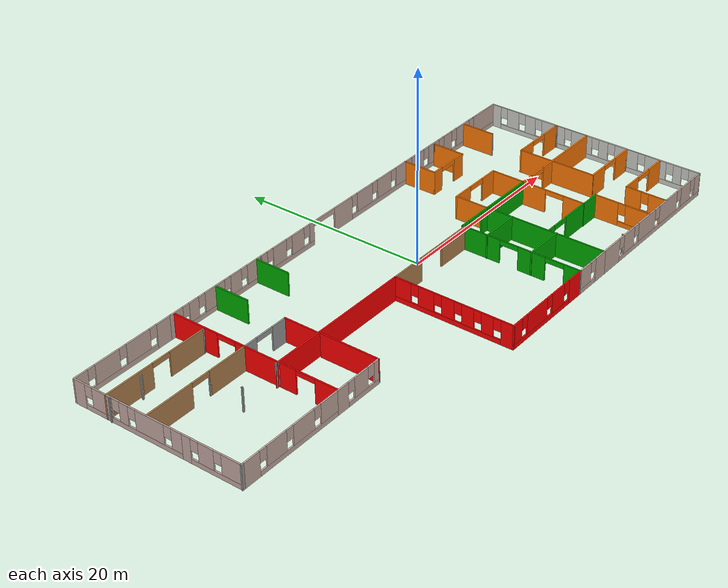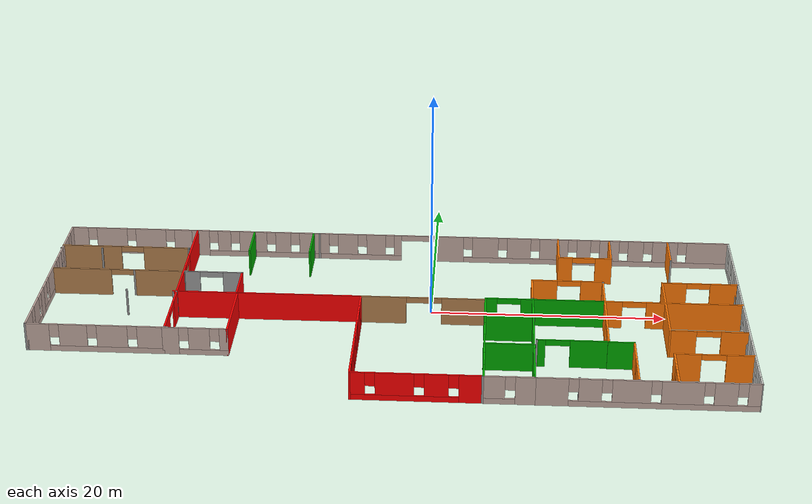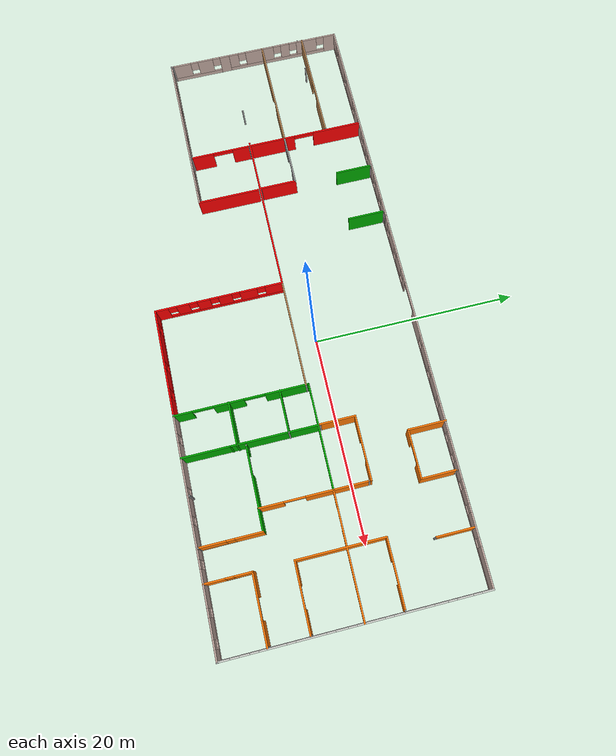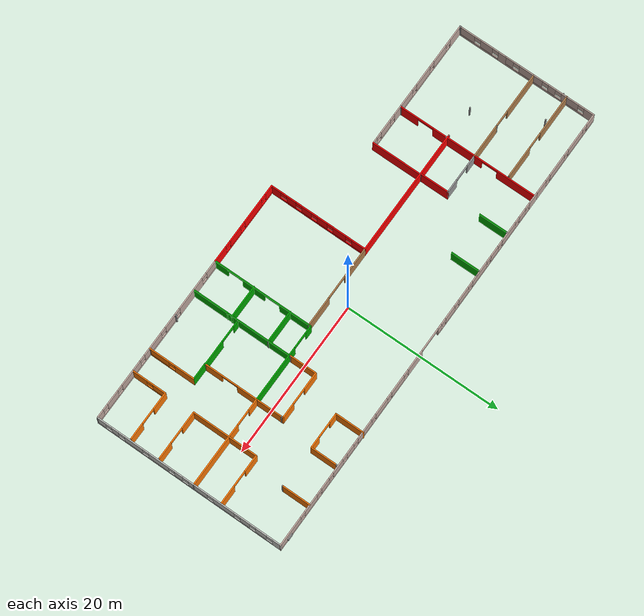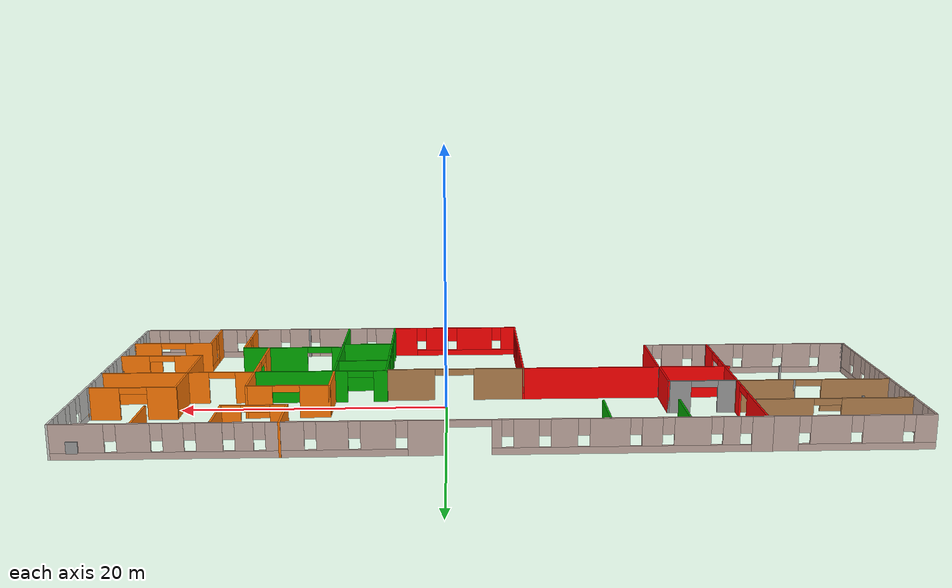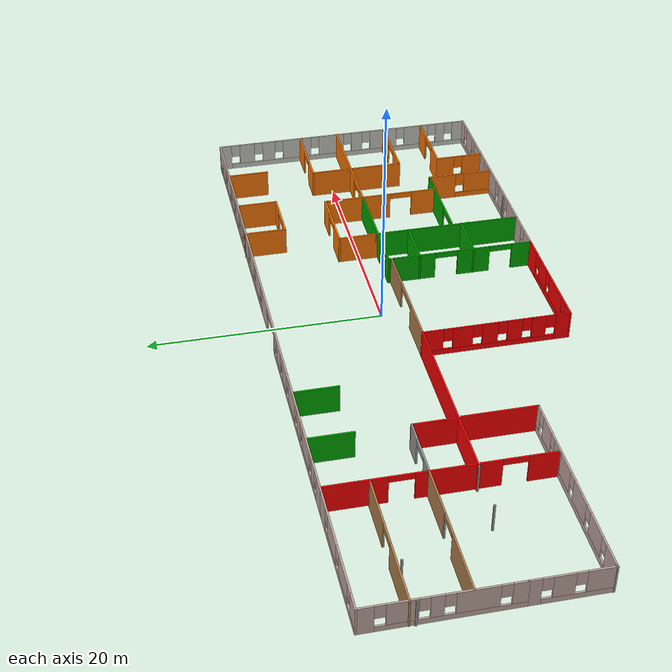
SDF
<?xml version='1.0'?>
<sdf version='1.6'>
  <model name='FloorPlan'>
    <pose frame=''>-3.5402 -2.3631 0 0 -0 0</pose>
    <link name='Wall_0'>
      <pose frame=''>5.59242 12.1499 0 0 -0 7e-06</pose>
      <visual name='Wall_0_Visual_0'>
        <pose frame=''>-23.5744 0 1.25 0 -0 0</pose>
        <geometry>
          <box>
            <size>1.60129 0.15 2.5</size>
          </box>
        </geometry>
        <material>
          <script>
            <uri>file://media/materials/scripts/gazebo.material</uri>
            <name>Gazebo/Grey</name>
          </script>
          <ambient>0.760784 0.662745 0.627451 1</ambient>
        </material>
        <meta>
          <layer>0</layer>
        </meta>
      </visual>
      <collision name='Wall_0_Collision_0'>
        <geometry>
          <box>
            <size>1.60129 0.15 2.5</size>
          </box>
        </geometry>
        <pose frame=''>-23.5744 0 1.25 0 -0 0</pose>
      </collision>
      <visual name='Wall_0_Visual_1'>
        <pose frame=''>-0.824166 0 1.25 0 -0 0</pose>
        <geometry>
          <box>
            <size>2.64767 0.15 2.5</size>
          </box>
        </geometry>
        <material>
          <script>
            <uri>file://media/materials/scripts/gazebo.material</uri>
            <name>Gazebo/Grey</name>
          </script>
          <ambient>0.760784 0.662745 0.627451 1</ambient>
        </material>
        <meta>
          <layer>0</layer>
        </meta>
      </visual>
      <collision name='Wall_0_Collision_1'>
        <geometry>
          <box>
            <size>2.64767 0.15 2.5</size>
          </box>
        </geometry>
        <pose frame=''>-0.824166 0 1.25 0 -0 0</pose>
      </collision>
      <visual name='Wall_0_Visual_2'>
        <pose frame=''>-13.9609 0 0.25 0 -0 0</pose>
        <geometry>
          <box>
            <size>17.6257 0.15 0.5</size>
          </box>
        </geometry>
        <material>
          <script>
            <uri>file://media/materials/scripts/gazebo.material</uri>
            <name>Gazebo/Grey</name>
          </script>
          <ambient>0.760784 0.662745 0.627451 1</ambient>
        </material>
        <meta>
          <layer>0</layer>
        </meta>
      </visual>
      <collision name='Wall_0_Collision_2'>
        <geometry>
          <box>
            <size>17.6257 0.15 0.5</size>
          </box>
        </geometry>
        <pose frame=''>-13.9609 0 0.25 0 -0 0</pose>
      </collision>
      <visual name='Wall_0_Visual_3'>
        <pose frame=''>12.4373 0 0.25 0 -0 0</pose>
        <geometry>
          <box>
            <size>23.8753 0.15 0.5</size>
          </box>
        </geometry>
        <material>
          <script>
            <uri>file://media/materials/scripts/gazebo.material</uri>
            <name>Gazebo/Grey</name>
          </script>
          <ambient>0.760784 0.662745 0.627451 1</ambient>
        </material>
        <meta>
          <layer>0</layer>
        </meta>
      </visual>
      <collision name='Wall_0_Collision_3'>
        <geometry>
          <box>
            <size>23.8753 0.15 0.5</size>
          </box>
        </geometry>
        <pose frame=''>12.4373 0 0.25 0 -0 0</pose>
      </collision>
      <visual name='Wall_0_Visual_4'>
        <pose frame=''>-21.3839 0 1.5 0 -0 0</pose>
        <geometry>
          <box>
            <size>1.17957 0.15 2</size>
          </box>
        </geometry>
        <material>
          <script>
            <uri>file://media/materials/scripts/gazebo.material</uri>
            <name>Gazebo/Grey</name>
          </script>
          <ambient>0.760784 0.662745 0.627451 1</ambient>
        </material>
        <meta>
          <layer>0</layer>
        </meta>
      </visual>
      <collision name='Wall_0_Collision_4'>
        <geometry>
          <box>
            <size>1.17957 0.15 2</size>
          </box>
        </geometry>
        <pose frame=''>-21.3839 0 1.5 0 -0 0</pose>
      </collision>
      <visual name='Wall_0_Visual_5'>
        <pose frame=''>-18.7356 0 1.5 0 -0 0</pose>
        <geometry>
          <box>
            <size>2.51713 0.15 2</size>
          </box>
        </geometry>
        <material>
          <script>
            <uri>file://media/materials/scripts/gazebo.material</uri>
            <name>Gazebo/Grey</name>
          </script>
          <ambient>0.760784 0.662745 0.627451 1</ambient>
        </material>
        <meta>
          <layer>0</layer>
        </meta>
      </visual>
      <collision name='Wall_0_Collision_5'>
        <geometry>
          <box>
            <size>2.51713 0.15 2</size>
          </box>
        </geometry>
        <pose frame=''>-18.7356 0 1.5 0 -0 0</pose>
      </collision>
      <visual name='Wall_0_Visual_6'>
        <pose frame=''>-15.9802 0 1.5 0 -0 0</pose>
        <geometry>
          <box>
            <size>1.39358 0.15 2</size>
          </box>
        </geometry>
        <material>
          <script>
            <uri>file://media/materials/scripts/gazebo.material</uri>
            <name>Gazebo/Grey</name>
          </script>
          <ambient>0.760784 0.662745 0.627451 1</ambient>
        </material>
        <meta>
          <layer>0</layer>
        </meta>
      </visual>
      <collision name='Wall_0_Collision_6'>
        <geometry>
          <box>
            <size>1.39358 0.15 2</size>
          </box>
        </geometry>
        <pose frame=''>-15.9802 0 1.5 0 -0 0</pose>
      </collision>
      <visual name='Wall_0_Visual_7'>
        <pose frame=''>-13.1179 0 1.5 0 -0 0</pose>
        <geometry>
          <box>
            <size>2.73113 0.15 2</size>
          </box>
        </geometry>
        <material>
          <script>
            <uri>file://media/materials/scripts/gazebo.material</uri>
            <name>Gazebo/Grey</name>
          </script>
          <ambient>0.760784 0.662745 0.627451 1</ambient>
        </material>
        <meta>
          <layer>0</layer>
        </meta>
      </visual>
      <collision name='Wall_0_Collision_7'>
        <geometry>
          <box>
            <size>2.73113 0.15 2</size>
          </box>
        </geometry>
        <pose frame=''>-13.1179 0 1.5 0 -0 0</pose>
      </collision>
      <visual name='Wall_0_Visual_8'>
        <pose frame=''>-10.0415 0 1.5 0 -0 0</pose>
        <geometry>
          <box>
            <size>1.8216 0.15 2</size>
          </box>
        </geometry>
        <material>
          <script>
            <uri>file://media/materials/scripts/gazebo.material</uri>
            <name>Gazebo/Grey</name>
          </script>
          <ambient>0.760784 0.662745 0.627451 1</ambient>
        </material>
        <meta>
          <layer>0</layer>
        </meta>
      </visual>
      <collision name='Wall_0_Collision_8'>
        <geometry>
          <box>
            <size>1.8216 0.15 2</size>
          </box>
        </geometry>
        <pose frame=''>-10.0415 0 1.5 0 -0 0</pose>
      </collision>
      <visual name='Wall_0_Visual_9'>
        <pose frame=''>-7.4734 0 1.5 0 -0 0</pose>
        <geometry>
          <box>
            <size>1.7146 0.15 2</size>
          </box>
        </geometry>
        <material>
          <script>
            <uri>file://media/materials/scripts/gazebo.material</uri>
            <name>Gazebo/Grey</name>
          </script>
          <ambient>0.760784 0.662745 0.627451 1</ambient>
        </material>
        <meta>
          <layer>0</layer>
        </meta>
      </visual>
      <collision name='Wall_0_Collision_9'>
        <geometry>
          <box>
            <size>1.7146 0.15 2</size>
          </box>
        </geometry>
        <pose frame=''>-7.4734 0 1.5 0 -0 0</pose>
      </collision>
      <visual name='Wall_0_Visual_10'>
        <pose frame=''>-5.48205 0 1.5 0 -0 0</pose>
        <geometry>
          <box>
            <size>0.668097 0.15 2</size>
          </box>
        </geometry>
        <material>
          <script>
            <uri>file://media/materials/scripts/gazebo.material</uri>
            <name>Gazebo/Grey</name>
          </script>
          <ambient>0.760784 0.662745 0.627451 1</ambient>
        </material>
        <meta>
          <layer>0</layer>
        </meta>
      </visual>
      <collision name='Wall_0_Collision_10'>
        <geometry>
          <box>
            <size>0.668097 0.15 2</size>
          </box>
        </geometry>
        <pose frame=''>-5.48205 0 1.5 0 -0 0</pose>
      </collision>
      <visual name='Wall_0_Visual_11'>
        <pose frame=''>-5.48205 0 1.5 0 -0 0</pose>
        <geometry>
          <box>
            <size>0.668097 0.15 2</size>
          </box>
        </geometry>
        <material>
          <script>
            <uri>file://media/materials/scripts/gazebo.material</uri>
            <name>Gazebo/Grey</name>
          </script>
          <ambient>0.760784 0.662745 0.627451 1</ambient>
        </material>
        <meta>
          <layer>0</layer>
        </meta>
      </visual>
      <collision name='Wall_0_Collision_11'>
        <geometry>
          <box>
            <size>0.668097 0.15 2</size>
          </box>
        </geometry>
        <pose frame=''>-5.48205 0 1.5 0 -0 0</pose>
      </collision>
      <visual name='Wall_0_Visual_12'>
        <pose frame=''>2.47798 0 1.5 0 -0 0</pose>
        <geometry>
          <box>
            <size>2.35662 0.15 2</size>
          </box>
        </geometry>
        <material>
          <script>
            <uri>file://media/materials/scripts/gazebo.material</uri>
            <name>Gazebo/Grey</name>
          </script>
          <ambient>0.760784 0.662745 0.627451 1</ambient>
        </material>
        <meta>
          <layer>0</layer>
        </meta>
      </visual>
      <collision name='Wall_0_Collision_12'>
        <geometry>
          <box>
            <size>2.35662 0.15 2</size>
          </box>
        </geometry>
        <pose frame=''>2.47798 0 1.5 0 -0 0</pose>
      </collision>
      <visual name='Wall_0_Visual_13'>
        <pose frame=''>5.5276 0 1.5 0 -0 0</pose>
        <geometry>
          <box>
            <size>2.14261 0.15 2</size>
          </box>
        </geometry>
        <material>
          <script>
            <uri>file://media/materials/scripts/gazebo.material</uri>
            <name>Gazebo/Grey</name>
          </script>
          <ambient>0.760784 0.662745 0.627451 1</ambient>
        </material>
        <meta>
          <layer>0</layer>
        </meta>
      </visual>
      <collision name='Wall_0_Collision_13'>
        <geometry>
          <box>
            <size>2.14261 0.15 2</size>
          </box>
        </geometry>
        <pose frame=''>5.5276 0 1.5 0 -0 0</pose>
      </collision>
      <visual name='Wall_0_Visual_14'>
        <pose frame=''>8.68422 0 1.5 0 -0 0</pose>
        <geometry>
          <box>
            <size>2.57063 0.15 2</size>
          </box>
        </geometry>
        <material>
          <script>
            <uri>file://media/materials/scripts/gazebo.material</uri>
            <name>Gazebo/Grey</name>
          </script>
          <ambient>0.760784 0.662745 0.627451 1</ambient>
        </material>
        <meta>
          <layer>0</layer>
        </meta>
      </visual>
      <collision name='Wall_0_Collision_14'>
        <geometry>
          <box>
            <size>2.57063 0.15 2</size>
          </box>
        </geometry>
        <pose frame=''>8.68422 0 1.5 0 -0 0</pose>
      </collision>
      <visual name='Wall_0_Visual_15'>
        <pose frame=''>11.3861 0 1.5 0 -0 0</pose>
        <geometry>
          <box>
            <size>1.23308 0.15 2</size>
          </box>
        </geometry>
        <material>
          <script>
            <uri>file://media/materials/scripts/gazebo.material</uri>
            <name>Gazebo/Grey</name>
          </script>
          <ambient>0.760784 0.662745 0.627451 1</ambient>
        </material>
        <meta>
          <layer>0</layer>
        </meta>
      </visual>
      <collision name='Wall_0_Collision_15'>
        <geometry>
          <box>
            <size>1.23308 0.15 2</size>
          </box>
        </geometry>
        <pose frame=''>11.3861 0 1.5 0 -0 0</pose>
      </collision>
      <visual name='Wall_0_Visual_16'>
        <pose frame=''>13.6867 0 1.5 0 -0 0</pose>
        <geometry>
          <box>
            <size>1.7681 0.15 2</size>
          </box>
        </geometry>
        <material>
          <script>
            <uri>file://media/materials/scripts/gazebo.material</uri>
            <name>Gazebo/Grey</name>
          </script>
          <ambient>0.760784 0.662745 0.627451 1</ambient>
        </material>
        <meta>
          <layer>0</layer>
        </meta>
      </visual>
      <collision name='Wall_0_Collision_16'>
        <geometry>
          <box>
            <size>1.7681 0.15 2</size>
          </box>
        </geometry>
        <pose frame=''>13.6867 0 1.5 0 -0 0</pose>
      </collision>
      <visual name='Wall_0_Visual_17'>
        <pose frame=''>16.0675 0 1.5 0 -0 0</pose>
        <geometry>
          <box>
            <size>1.39358 0.15 2</size>
          </box>
        </geometry>
        <material>
          <script>
            <uri>file://media/materials/scripts/gazebo.material</uri>
            <name>Gazebo/Grey</name>
          </script>
          <ambient>0.760784 0.662745 0.627451 1</ambient>
        </material>
        <meta>
          <layer>0</layer>
        </meta>
      </visual>
      <collision name='Wall_0_Collision_17'>
        <geometry>
          <box>
            <size>1.39358 0.15 2</size>
          </box>
        </geometry>
        <pose frame=''>16.0675 0 1.5 0 -0 0</pose>
      </collision>
      <visual name='Wall_0_Visual_18'>
        <pose frame=''>18.6891 0 1.5 0 -0 0</pose>
        <geometry>
          <box>
            <size>2.24962 0.15 2</size>
          </box>
        </geometry>
        <material>
          <script>
            <uri>file://media/materials/scripts/gazebo.material</uri>
            <name>Gazebo/Grey</name>
          </script>
          <ambient>0.760784 0.662745 0.627451 1</ambient>
        </material>
        <meta>
          <layer>0</layer>
        </meta>
      </visual>
      <collision name='Wall_0_Collision_18'>
        <geometry>
          <box>
            <size>2.24962 0.15 2</size>
          </box>
        </geometry>
        <pose frame=''>18.6891 0 1.5 0 -0 0</pose>
      </collision>
      <visual name='Wall_0_Visual_19'>
        <pose frame=''>22.4945 0 1.5 0 -0 0</pose>
        <geometry>
          <box>
            <size>3.7611 0.15 2</size>
          </box>
        </geometry>
        <material>
          <script>
            <uri>file://media/materials/scripts/gazebo.material</uri>
            <name>Gazebo/Grey</name>
          </script>
          <ambient>0.760784 0.662745 0.627451 1</ambient>
        </material>
        <meta>
          <layer>0</layer>
        </meta>
      </visual>
      <collision name='Wall_0_Collision_19'>
        <geometry>
          <box>
            <size>3.7611 0.15 2</size>
          </box>
        </geometry>
        <pose frame=''>22.4945 0 1.5 0 -0 0</pose>
      </collision>
      <visual name='Wall_0_Visual_20'>
        <pose frame=''>-22.3737 0 1.9 0 -0 0</pose>
        <geometry>
          <box>
            <size>0.8 0.15 1.2</size>
          </box>
        </geometry>
        <material>
          <script>
            <uri>file://media/materials/scripts/gazebo.material</uri>
            <name>Gazebo/Grey</name>
          </script>
          <ambient>0.760784 0.662745 0.627451 1</ambient>
        </material>
        <meta>
          <layer>0</layer>
        </meta>
      </visual>
      <collision name='Wall_0_Collision_20'>
        <geometry>
          <box>
            <size>0.8 0.15 1.2</size>
          </box>
        </geometry>
        <pose frame=''>-22.3737 0 1.9 0 -0 0</pose>
      </collision>
      <visual name='Wall_0_Visual_21'>
        <pose frame=''>0.89967 0 1.9 0 -0 0</pose>
        <geometry>
          <box>
            <size>0.8 0.15 1.2</size>
          </box>
        </geometry>
        <material>
          <script>
            <uri>file://media/materials/scripts/gazebo.material</uri>
            <name>Gazebo/Grey</name>
          </script>
          <ambient>0.760784 0.662745 0.627451 1</ambient>
        </material>
        <meta>
          <layer>0</layer>
        </meta>
      </visual>
      <collision name='Wall_0_Collision_21'>
        <geometry>
          <box>
            <size>0.8 0.15 1.2</size>
          </box>
        </geometry>
        <pose frame=''>0.89967 0 1.9 0 -0 0</pose>
      </collision>
      <visual name='Wall_0_Visual_22'>
        <pose frame=''>-20.3941 0 1.9 0 -0 0</pose>
        <geometry>
          <box>
            <size>0.8 0.15 1.2</size>
          </box>
        </geometry>
        <material>
          <script>
            <uri>file://media/materials/scripts/gazebo.material</uri>
            <name>Gazebo/Grey</name>
          </script>
          <ambient>0.760784 0.662745 0.627451 1</ambient>
        </material>
        <meta>
          <layer>0</layer>
        </meta>
      </visual>
      <collision name='Wall_0_Collision_22'>
        <geometry>
          <box>
            <size>0.8 0.15 1.2</size>
          </box>
        </geometry>
        <pose frame=''>-20.3941 0 1.9 0 -0 0</pose>
      </collision>
      <visual name='Wall_0_Visual_23'>
        <pose frame=''>-17.077 0 1.9 0 -0 0</pose>
        <geometry>
          <box>
            <size>0.8 0.15 1.2</size>
          </box>
        </geometry>
        <material>
          <script>
            <uri>file://media/materials/scripts/gazebo.material</uri>
            <name>Gazebo/Grey</name>
          </script>
          <ambient>0.760784 0.662745 0.627451 1</ambient>
        </material>
        <meta>
          <layer>0</layer>
        </meta>
      </visual>
      <collision name='Wall_0_Collision_23'>
        <geometry>
          <box>
            <size>0.8 0.15 1.2</size>
          </box>
        </geometry>
        <pose frame=''>-17.077 0 1.9 0 -0 0</pose>
      </collision>
      <visual name='Wall_0_Visual_24'>
        <pose frame=''>-14.8834 0 1.9 0 -0 0</pose>
        <geometry>
          <box>
            <size>0.8 0.15 1.2</size>
          </box>
        </geometry>
        <material>
          <script>
            <uri>file://media/materials/scripts/gazebo.material</uri>
            <name>Gazebo/Grey</name>
          </script>
          <ambient>0.760784 0.662745 0.627451 1</ambient>
        </material>
        <meta>
          <layer>0</layer>
        </meta>
      </visual>
      <collision name='Wall_0_Collision_24'>
        <geometry>
          <box>
            <size>0.8 0.15 1.2</size>
          </box>
        </geometry>
        <pose frame=''>-14.8834 0 1.9 0 -0 0</pose>
      </collision>
      <visual name='Wall_0_Visual_25'>
        <pose frame=''>-11.3523 0 1.9 0 -0 0</pose>
        <geometry>
          <box>
            <size>0.8 0.15 1.2</size>
          </box>
        </geometry>
        <material>
          <script>
            <uri>file://media/materials/scripts/gazebo.material</uri>
            <name>Gazebo/Grey</name>
          </script>
          <ambient>0.760784 0.662745 0.627451 1</ambient>
        </material>
        <meta>
          <layer>0</layer>
        </meta>
      </visual>
      <collision name='Wall_0_Collision_25'>
        <geometry>
          <box>
            <size>0.8 0.15 1.2</size>
          </box>
        </geometry>
        <pose frame=''>-11.3523 0 1.9 0 -0 0</pose>
      </collision>
      <visual name='Wall_0_Visual_26'>
        <pose frame=''>-8.7307 0 1.9 0 -0 0</pose>
        <geometry>
          <box>
            <size>0.8 0.15 1.2</size>
          </box>
        </geometry>
        <material>
          <script>
            <uri>file://media/materials/scripts/gazebo.material</uri>
            <name>Gazebo/Grey</name>
          </script>
          <ambient>0.760784 0.662745 0.627451 1</ambient>
        </material>
        <meta>
          <layer>0</layer>
        </meta>
      </visual>
      <collision name='Wall_0_Collision_26'>
        <geometry>
          <box>
            <size>0.8 0.15 1.2</size>
          </box>
        </geometry>
        <pose frame=''>-8.7307 0 1.9 0 -0 0</pose>
      </collision>
      <visual name='Wall_0_Visual_27'>
        <pose frame=''>-6.2161 0 1.9 0 -0 0</pose>
        <geometry>
          <box>
            <size>0.8 0.15 1.2</size>
          </box>
        </geometry>
        <material>
          <script>
            <uri>file://media/materials/scripts/gazebo.material</uri>
            <name>Gazebo/Grey</name>
          </script>
          <ambient>0.760784 0.662745 0.627451 1</ambient>
        </material>
        <meta>
          <layer>0</layer>
        </meta>
      </visual>
      <collision name='Wall_0_Collision_27'>
        <geometry>
          <box>
            <size>0.8 0.15 1.2</size>
          </box>
        </geometry>
        <pose frame=''>-6.2161 0 1.9 0 -0 0</pose>
      </collision>
      <visual name='Wall_0_Visual_28'>
        <pose frame=''>4.05629 0 1.9 0 -0 0</pose>
        <geometry>
          <box>
            <size>0.8 0.15 1.2</size>
          </box>
        </geometry>
        <material>
          <script>
            <uri>file://media/materials/scripts/gazebo.material</uri>
            <name>Gazebo/Grey</name>
          </script>
          <ambient>0.760784 0.662745 0.627451 1</ambient>
        </material>
        <meta>
          <layer>0</layer>
        </meta>
      </visual>
      <collision name='Wall_0_Collision_28'>
        <geometry>
          <box>
            <size>0.8 0.15 1.2</size>
          </box>
        </geometry>
        <pose frame=''>4.05629 0 1.9 0 -0 0</pose>
      </collision>
      <visual name='Wall_0_Visual_29'>
        <pose frame=''>6.9989 0 1.9 0 -0 0</pose>
        <geometry>
          <box>
            <size>0.8 0.15 1.2</size>
          </box>
        </geometry>
        <material>
          <script>
            <uri>file://media/materials/scripts/gazebo.material</uri>
            <name>Gazebo/Grey</name>
          </script>
          <ambient>0.760784 0.662745 0.627451 1</ambient>
        </material>
        <meta>
          <layer>0</layer>
        </meta>
      </visual>
      <collision name='Wall_0_Collision_29'>
        <geometry>
          <box>
            <size>0.8 0.15 1.2</size>
          </box>
        </geometry>
        <pose frame=''>6.9989 0 1.9 0 -0 0</pose>
      </collision>
      <visual name='Wall_0_Visual_30'>
        <pose frame=''>10.3695 0 1.9 0 -0 0</pose>
        <geometry>
          <box>
            <size>0.8 0.15 1.2</size>
          </box>
        </geometry>
        <material>
          <script>
            <uri>file://media/materials/scripts/gazebo.material</uri>
            <name>Gazebo/Grey</name>
          </script>
          <ambient>0.760784 0.662745 0.627451 1</ambient>
        </material>
        <meta>
          <layer>0</layer>
        </meta>
      </visual>
      <collision name='Wall_0_Collision_30'>
        <geometry>
          <box>
            <size>0.8 0.15 1.2</size>
          </box>
        </geometry>
        <pose frame=''>10.3695 0 1.9 0 -0 0</pose>
      </collision>
      <visual name='Wall_0_Visual_31'>
        <pose frame=''>12.4026 0 1.9 0 -0 0</pose>
        <geometry>
          <box>
            <size>0.8 0.15 1.2</size>
          </box>
        </geometry>
        <material>
          <script>
            <uri>file://media/materials/scripts/gazebo.material</uri>
            <name>Gazebo/Grey</name>
          </script>
          <ambient>0.760784 0.662745 0.627451 1</ambient>
        </material>
        <meta>
          <layer>0</layer>
        </meta>
      </visual>
      <collision name='Wall_0_Collision_31'>
        <geometry>
          <box>
            <size>0.8 0.15 1.2</size>
          </box>
        </geometry>
        <pose frame=''>12.4026 0 1.9 0 -0 0</pose>
      </collision>
      <visual name='Wall_0_Visual_32'>
        <pose frame=''>14.9707 0 1.9 0 -0 0</pose>
        <geometry>
          <box>
            <size>0.8 0.15 1.2</size>
          </box>
        </geometry>
        <material>
          <script>
            <uri>file://media/materials/scripts/gazebo.material</uri>
            <name>Gazebo/Grey</name>
          </script>
          <ambient>0.760784 0.662745 0.627451 1</ambient>
        </material>
        <meta>
          <layer>0</layer>
        </meta>
      </visual>
      <collision name='Wall_0_Collision_32'>
        <geometry>
          <box>
            <size>0.8 0.15 1.2</size>
          </box>
        </geometry>
        <pose frame=''>14.9707 0 1.9 0 -0 0</pose>
      </collision>
      <visual name='Wall_0_Visual_33'>
        <pose frame=''>17.1643 0 1.9 0 -0 0</pose>
        <geometry>
          <box>
            <size>0.8 0.15 1.2</size>
          </box>
        </geometry>
        <material>
          <script>
            <uri>file://media/materials/scripts/gazebo.material</uri>
            <name>Gazebo/Grey</name>
          </script>
          <ambient>0.760784 0.662745 0.627451 1</ambient>
        </material>
        <meta>
          <layer>0</layer>
        </meta>
      </visual>
      <collision name='Wall_0_Collision_33'>
        <geometry>
          <box>
            <size>0.8 0.15 1.2</size>
          </box>
        </geometry>
        <pose frame=''>17.1643 0 1.9 0 -0 0</pose>
      </collision>
      <visual name='Wall_0_Visual_34'>
        <pose frame=''>20.2139 0 1.9 0 -0 0</pose>
        <geometry>
          <box>
            <size>0.8 0.15 1.2</size>
          </box>
        </geometry>
        <material>
          <script>
            <uri>file://media/materials/scripts/gazebo.material</uri>
            <name>Gazebo/Grey</name>
          </script>
          <ambient>0.760784 0.662745 0.627451 1</ambient>
        </material>
        <meta>
          <layer>0</layer>
        </meta>
      </visual>
      <collision name='Wall_0_Collision_34'>
        <geometry>
          <box>
            <size>0.8 0.15 1.2</size>
          </box>
        </geometry>
        <pose frame=''>20.2139 0 1.9 0 -0 0</pose>
      </collision>
      <visual name='Wall_0_Visual_35'>
        <pose frame=''>-3.648 0 2.25 0 -0 0</pose>
        <geometry>
          <box>
            <size>3 0.15 0.5</size>
          </box>
        </geometry>
        <material>
          <script>
            <uri>file://media/materials/scripts/gazebo.material</uri>
            <name>Gazebo/Grey</name>
          </script>
          <ambient>0.760784 0.662745 0.627451 1</ambient>
        </material>
        <meta>
          <layer>0</layer>
        </meta>
      </visual>
      <collision name='Wall_0_Collision_35'>
        <geometry>
          <box>
            <size>3 0.15 0.5</size>
          </box>
        </geometry>
        <pose frame=''>-3.648 0 2.25 0 -0 0</pose>
      </collision>
      <visual name='Wall_0_Visual_36'>
        <pose frame=''>-3.648 0 2.25 0 -0 0</pose>
        <geometry>
          <box>
            <size>3 0.15 0.5</size>
          </box>
        </geometry>
        <material>
          <script>
            <uri>file://media/materials/scripts/gazebo.material</uri>
            <name>Gazebo/Grey</name>
          </script>
          <ambient>0.760784 0.662745 0.627451 1</ambient>
        </material>
        <meta>
          <layer>0</layer>
        </meta>
      </visual>
      <collision name='Wall_0_Collision_36'>
        <geometry>
          <box>
            <size>3 0.15 0.5</size>
          </box>
        </geometry>
        <pose frame=''>-3.648 0 2.25 0 -0 0</pose>
      </collision>
    </link>
    <link name='Wall_1'>
      <pose frame=''>29.8922 -0.024899 0 0 -0 -1.5708</pose>
      <visual name='Wall_1_Visual_0'>
        <pose frame=''>-11.6902 0 1.25 0 -0 0</pose>
        <geometry>
          <box>
            <size>1.11957 0.15 2.5</size>
          </box>
        </geometry>
        <material>
          <script>
            <uri>file://media/materials/scripts/gazebo.material</uri>
            <name>Gazebo/CeilingTiled</name>
          </script>
          <ambient>0.760784 0.662745 0.627451 1</ambient>
        </material>
        <meta>
          <layer>0</layer>
        </meta>
      </visual>
      <collision name='Wall_1_Collision_0'>
        <geometry>
          <box>
            <size>1.11957 0.15 2.5</size>
          </box>
        </geometry>
        <pose frame=''>-11.6902 0 1.25 0 -0 0</pose>
      </collision>
      <visual name='Wall_1_Visual_1'>
        <pose frame=''>0.559784 0 0.25 0 -0 0</pose>
        <geometry>
          <box>
            <size>23.3804 0.15 0.5</size>
          </box>
        </geometry>
        <material>
          <script>
            <uri>file://media/materials/scripts/gazebo.material</uri>
            <name>Gazebo/CeilingTiled</name>
          </script>
          <ambient>0.760784 0.662745 0.627451 1</ambient>
        </material>
        <meta>
          <layer>0</layer>
        </meta>
      </visual>
      <collision name='Wall_1_Collision_1'>
        <geometry>
          <box>
            <size>23.3804 0.15 0.5</size>
          </box>
        </geometry>
        <pose frame=''>0.559784 0 0.25 0 -0 0</pose>
      </collision>
      <visual name='Wall_1_Visual_2'>
        <pose frame=''>-9.60688 0 1.5 0 -0 0</pose>
        <geometry>
          <box>
            <size>1.44711 0.15 2</size>
          </box>
        </geometry>
        <material>
          <script>
            <uri>file://media/materials/scripts/gazebo.material</uri>
            <name>Gazebo/CeilingTiled</name>
          </script>
          <ambient>0.760784 0.662745 0.627451 1</ambient>
        </material>
        <meta>
          <layer>0</layer>
        </meta>
      </visual>
      <collision name='Wall_1_Collision_2'>
        <geometry>
          <box>
            <size>1.44711 0.15 2</size>
          </box>
        </geometry>
        <pose frame=''>-9.60688 0 1.5 0 -0 0</pose>
      </collision>
      <visual name='Wall_1_Visual_3'>
        <pose frame=''>-7.46678 0 1.5 0 -0 0</pose>
        <geometry>
          <box>
            <size>1.2331 0.15 2</size>
          </box>
        </geometry>
        <material>
          <script>
            <uri>file://media/materials/scripts/gazebo.material</uri>
            <name>Gazebo/CeilingTiled</name>
          </script>
          <ambient>0.760784 0.662745 0.627451 1</ambient>
        </material>
        <meta>
          <layer>0</layer>
        </meta>
      </visual>
      <collision name='Wall_1_Collision_3'>
        <geometry>
          <box>
            <size>1.2331 0.15 2</size>
          </box>
        </geometry>
        <pose frame=''>-7.46678 0 1.5 0 -0 0</pose>
      </collision>
      <visual name='Wall_1_Visual_4'>
        <pose frame=''>-4.6579 0 1.5 0 -0 0</pose>
        <geometry>
          <box>
            <size>2.78467 0.15 2</size>
          </box>
        </geometry>
        <material>
          <script>
            <uri>file://media/materials/scripts/gazebo.material</uri>
            <name>Gazebo/CeilingTiled</name>
          </script>
          <ambient>0.760784 0.662745 0.627451 1</ambient>
        </material>
        <meta>
          <layer>0</layer>
        </meta>
      </visual>
      <collision name='Wall_1_Collision_4'>
        <geometry>
          <box>
            <size>2.78467 0.15 2</size>
          </box>
        </geometry>
        <pose frame=''>-4.6579 0 1.5 0 -0 0</pose>
      </collision>
      <visual name='Wall_1_Visual_5'>
        <pose frame=''>-1.23374 0 1.5 0 -0 0</pose>
        <geometry>
          <box>
            <size>2.46365 0.15 2</size>
          </box>
        </geometry>
        <material>
          <script>
            <uri>file://media/materials/scripts/gazebo.material</uri>
            <name>Gazebo/CeilingTiled</name>
          </script>
          <ambient>0.760784 0.662745 0.627451 1</ambient>
        </material>
        <meta>
          <layer>0</layer>
        </meta>
      </visual>
      <collision name='Wall_1_Collision_5'>
        <geometry>
          <box>
            <size>2.46365 0.15 2</size>
          </box>
        </geometry>
        <pose frame=''>-1.23374 0 1.5 0 -0 0</pose>
      </collision>
      <visual name='Wall_1_Visual_6'>
        <pose frame=''>1.33438 0 1.5 0 -0 0</pose>
        <geometry>
          <box>
            <size>1.07259 0.15 2</size>
          </box>
        </geometry>
        <material>
          <script>
            <uri>file://media/materials/scripts/gazebo.material</uri>
            <name>Gazebo/CeilingTiled</name>
          </script>
          <ambient>0.760784 0.662745 0.627451 1</ambient>
        </material>
        <meta>
          <layer>0</layer>
        </meta>
      </visual>
      <collision name='Wall_1_Collision_6'>
        <geometry>
          <box>
            <size>1.07259 0.15 2</size>
          </box>
        </geometry>
        <pose frame=''>1.33438 0 1.5 0 -0 0</pose>
      </collision>
      <visual name='Wall_1_Visual_7'>
        <pose frame=''>4.00951 0 1.5 0 -0 0</pose>
        <geometry>
          <box>
            <size>2.67766 0.15 2</size>
          </box>
        </geometry>
        <material>
          <script>
            <uri>file://media/materials/scripts/gazebo.material</uri>
            <name>Gazebo/CeilingTiled</name>
          </script>
          <ambient>0.760784 0.662745 0.627451 1</ambient>
        </material>
        <meta>
          <layer>0</layer>
        </meta>
      </visual>
      <collision name='Wall_1_Collision_7'>
        <geometry>
          <box>
            <size>2.67766 0.15 2</size>
          </box>
        </geometry>
        <pose frame=''>4.00951 0 1.5 0 -0 0</pose>
      </collision>
      <visual name='Wall_1_Visual_8'>
        <pose frame=''>7.35341 0 1.5 0 -0 0</pose>
        <geometry>
          <box>
            <size>2.41015 0.15 2</size>
          </box>
        </geometry>
        <material>
          <script>
            <uri>file://media/materials/scripts/gazebo.material</uri>
            <name>Gazebo/CeilingTiled</name>
          </script>
          <ambient>0.760784 0.662745 0.627451 1</ambient>
        </material>
        <meta>
          <layer>0</layer>
        </meta>
      </visual>
      <collision name='Wall_1_Collision_8'>
        <geometry>
          <box>
            <size>2.41015 0.15 2</size>
          </box>
        </geometry>
        <pose frame=''>7.35341 0 1.5 0 -0 0</pose>
      </collision>
      <visual name='Wall_1_Visual_9'>
        <pose frame=''>9.81453 0 1.5 0 -0 0</pose>
        <geometry>
          <box>
            <size>0.91208 0.15 2</size>
          </box>
        </geometry>
        <material>
          <script>
            <uri>file://media/materials/scripts/gazebo.material</uri>
            <name>Gazebo/CeilingTiled</name>
          </script>
          <ambient>0.760784 0.662745 0.627451 1</ambient>
        </material>
        <meta>
          <layer>0</layer>
        </meta>
      </visual>
      <collision name='Wall_1_Collision_9'>
        <geometry>
          <box>
            <size>0.91208 0.15 2</size>
          </box>
        </geometry>
        <pose frame=''>9.81453 0 1.5 0 -0 0</pose>
      </collision>
      <visual name='Wall_1_Visual_10'>
        <pose frame=''>11.6603 0 1.5 0 -0 0</pose>
        <geometry>
          <box>
            <size>1.17943 0.15 2</size>
          </box>
        </geometry>
        <material>
          <script>
            <uri>file://media/materials/scripts/gazebo.material</uri>
            <name>Gazebo/CeilingTiled</name>
          </script>
          <ambient>0.760784 0.662745 0.627451 1</ambient>
        </material>
        <meta>
          <layer>0</layer>
        </meta>
      </visual>
      <collision name='Wall_1_Collision_10'>
        <geometry>
          <box>
            <size>1.17943 0.15 2</size>
          </box>
        </geometry>
        <pose frame=''>11.6603 0 1.5 0 -0 0</pose>
      </collision>
      <visual name='Wall_1_Visual_11'>
        <pose frame=''>-10.7304 0 1.9 0 -0 0</pose>
        <geometry>
          <box>
            <size>0.8 0.15 1.2</size>
          </box>
        </geometry>
        <material>
          <script>
            <uri>file://media/materials/scripts/gazebo.material</uri>
            <name>Gazebo/CeilingTiled</name>
          </script>
          <ambient>0.760784 0.662745 0.627451 1</ambient>
        </material>
        <meta>
          <layer>0</layer>
        </meta>
      </visual>
      <collision name='Wall_1_Collision_11'>
        <geometry>
          <box>
            <size>0.8 0.15 1.2</size>
          </box>
        </geometry>
        <pose frame=''>-10.7304 0 1.9 0 -0 0</pose>
      </collision>
      <visual name='Wall_1_Visual_12'>
        <pose frame=''>-8.48333 0 1.9 0 -0 0</pose>
        <geometry>
          <box>
            <size>0.8 0.15 1.2</size>
          </box>
        </geometry>
        <material>
          <script>
            <uri>file://media/materials/scripts/gazebo.material</uri>
            <name>Gazebo/CeilingTiled</name>
          </script>
          <ambient>0.760784 0.662745 0.627451 1</ambient>
        </material>
        <meta>
          <layer>0</layer>
        </meta>
      </visual>
      <collision name='Wall_1_Collision_12'>
        <geometry>
          <box>
            <size>0.8 0.15 1.2</size>
          </box>
        </geometry>
        <pose frame=''>-8.48333 0 1.9 0 -0 0</pose>
      </collision>
      <visual name='Wall_1_Visual_13'>
        <pose frame=''>-6.45023 0 1.9 0 -0 0</pose>
        <geometry>
          <box>
            <size>0.8 0.15 1.2</size>
          </box>
        </geometry>
        <material>
          <script>
            <uri>file://media/materials/scripts/gazebo.material</uri>
            <name>Gazebo/CeilingTiled</name>
          </script>
          <ambient>0.760784 0.662745 0.627451 1</ambient>
        </material>
        <meta>
          <layer>0</layer>
        </meta>
      </visual>
      <collision name='Wall_1_Collision_13'>
        <geometry>
          <box>
            <size>0.8 0.15 1.2</size>
          </box>
        </geometry>
        <pose frame=''>-6.45023 0 1.9 0 -0 0</pose>
      </collision>
      <visual name='Wall_1_Visual_14'>
        <pose frame=''>-2.86557 0 1.9 0 -0 0</pose>
        <geometry>
          <box>
            <size>0.8 0.15 1.2</size>
          </box>
        </geometry>
        <material>
          <script>
            <uri>file://media/materials/scripts/gazebo.material</uri>
            <name>Gazebo/CeilingTiled</name>
          </script>
          <ambient>0.760784 0.662745 0.627451 1</ambient>
        </material>
        <meta>
          <layer>0</layer>
        </meta>
      </visual>
      <collision name='Wall_1_Collision_14'>
        <geometry>
          <box>
            <size>0.8 0.15 1.2</size>
          </box>
        </geometry>
        <pose frame=''>-2.86557 0 1.9 0 -0 0</pose>
      </collision>
      <visual name='Wall_1_Visual_15'>
        <pose frame=''>0.398088 0 1.9 0 -0 0</pose>
        <geometry>
          <box>
            <size>0.8 0.15 1.2</size>
          </box>
        </geometry>
        <material>
          <script>
            <uri>file://media/materials/scripts/gazebo.material</uri>
            <name>Gazebo/CeilingTiled</name>
          </script>
          <ambient>0.760784 0.662745 0.627451 1</ambient>
        </material>
        <meta>
          <layer>0</layer>
        </meta>
      </visual>
      <collision name='Wall_1_Collision_15'>
        <geometry>
          <box>
            <size>0.8 0.15 1.2</size>
          </box>
        </geometry>
        <pose frame=''>0.398088 0 1.9 0 -0 0</pose>
      </collision>
      <visual name='Wall_1_Visual_16'>
        <pose frame=''>2.27068 0 1.9 0 -0 0</pose>
        <geometry>
          <box>
            <size>0.8 0.15 1.2</size>
          </box>
        </geometry>
        <material>
          <script>
            <uri>file://media/materials/scripts/gazebo.material</uri>
            <name>Gazebo/CeilingTiled</name>
          </script>
          <ambient>0.760784 0.662745 0.627451 1</ambient>
        </material>
        <meta>
          <layer>0</layer>
        </meta>
      </visual>
      <collision name='Wall_1_Collision_16'>
        <geometry>
          <box>
            <size>0.8 0.15 1.2</size>
          </box>
        </geometry>
        <pose frame=''>2.27068 0 1.9 0 -0 0</pose>
      </collision>
      <visual name='Wall_1_Visual_17'>
        <pose frame=''>5.74834 0 1.9 0 -0 0</pose>
        <geometry>
          <box>
            <size>0.8 0.15 1.2</size>
          </box>
        </geometry>
        <material>
          <script>
            <uri>file://media/materials/scripts/gazebo.material</uri>
            <name>Gazebo/CeilingTiled</name>
          </script>
          <ambient>0.760784 0.662745 0.627451 1</ambient>
        </material>
        <meta>
          <layer>0</layer>
        </meta>
      </visual>
      <collision name='Wall_1_Collision_17'>
        <geometry>
          <box>
            <size>0.8 0.15 1.2</size>
          </box>
        </geometry>
        <pose frame=''>5.74834 0 1.9 0 -0 0</pose>
      </collision>
      <visual name='Wall_1_Visual_18'>
        <pose frame=''>8.95849 0 1.9 0 -0 0</pose>
        <geometry>
          <box>
            <size>0.8 0.15 1.2</size>
          </box>
        </geometry>
        <material>
          <script>
            <uri>file://media/materials/scripts/gazebo.material</uri>
            <name>Gazebo/CeilingTiled</name>
          </script>
          <ambient>0.760784 0.662745 0.627451 1</ambient>
        </material>
        <meta>
          <layer>0</layer>
        </meta>
      </visual>
      <collision name='Wall_1_Collision_18'>
        <geometry>
          <box>
            <size>0.8 0.15 1.2</size>
          </box>
        </geometry>
        <pose frame=''>8.95849 0 1.9 0 -0 0</pose>
      </collision>
      <visual name='Wall_1_Visual_19'>
        <pose frame=''>10.6706 0 1.9 0 -0 0</pose>
        <geometry>
          <box>
            <size>0.8 0.15 1.2</size>
          </box>
        </geometry>
        <material>
          <script>
            <uri>file://media/materials/scripts/gazebo.material</uri>
            <name>Gazebo/CeilingTiled</name>
          </script>
          <ambient>0.760784 0.662745 0.627451 1</ambient>
        </material>
        <meta>
          <layer>0</layer>
        </meta>
      </visual>
      <collision name='Wall_1_Collision_19'>
        <geometry>
          <box>
            <size>0.8 0.15 1.2</size>
          </box>
        </geometry>
        <pose frame=''>10.6706 0 1.9 0 -0 0</pose>
      </collision>
    </link>
    <link name='Wall_101'>
      <collision name='Wall_101_Collision'>
        <geometry>
          <box>
            <size>13 0.15 2.5</size>
          </box>
        </geometry>
        <pose frame=''>0 0 1.25 0 -0 0</pose>
      </collision>
      <visual name='Wall_101_Visual'>
        <pose frame=''>0 0 1.25 0 -0 0</pose>
        <geometry>
          <box>
            <size>13 0.15 2.5</size>
          </box>
        </geometry>
        <material>
          <script>
            <uri>file://media/materials/scripts/gazebo.material</uri>
            <name>Gazebo/Grey</name>
          </script>
          <ambient>0 0.666667 0 1</ambient>
        </material>
        <meta>
          <layer>0</layer>
        </meta>
      </visual>
      <pose frame=''>12.2171 -5.77826 0 0 -0 -1.5708</pose>
    </link>
    <link name='Wall_102'>
      <collision name='Wall_102_Collision'>
        <geometry>
          <box>
            <size>0.15 0.15 2.5</size>
          </box>
        </geometry>
        <pose frame=''>0 0 1.25 0 -0 0</pose>
      </collision>
      <visual name='Wall_102_Visual'>
        <pose frame=''>0 0 1.25 0 -0 0</pose>
        <geometry>
          <box>
            <size>0.15 0.15 2.5</size>
          </box>
        </geometry>
        <material>
          <script>
            <uri>file://media/materials/scripts/gazebo.material</uri>
            <name>Gazebo/Grey</name>
          </script>
          <ambient>1 1 1 1</ambient>
        </material>
        <meta>
          <layer>0</layer>
        </meta>
      </visual>
      <pose frame=''>12.2171 -12.2033 0 0 -0 0</pose>
    </link>
    <link name='Wall_103'>
      <pose frame=''>10.1671 -12.2033 0 0 -0 3.14159</pose>
      <visual name='Wall_103_Visual_0'>
        <pose frame=''>-1.32445 0 1.25 0 -0 0</pose>
        <geometry>
          <box>
            <size>1.60109 0.15 2.5</size>
          </box>
        </geometry>
        <material>
          <script>
            <uri>file://media/materials/scripts/gazebo.material</uri>
            <name>Gazebo/Grey</name>
          </script>
          <ambient>0.760784 0.662745 0.627451 1</ambient>
        </material>
        <meta>
          <layer>0</layer>
        </meta>
      </visual>
      <collision name='Wall_103_Collision_0'>
        <geometry>
          <box>
            <size>1.60109 0.15 2.5</size>
          </box>
        </geometry>
        <pose frame=''>-1.32445 0 1.25 0 -0 0</pose>
      </collision>
      <visual name='Wall_103_Visual_1'>
        <pose frame=''>0.800545 0 0.25 0 -0 0</pose>
        <geometry>
          <box>
            <size>2.64891 0.15 0.5</size>
          </box>
        </geometry>
        <material>
          <script>
            <uri>file://media/materials/scripts/gazebo.material</uri>
            <name>Gazebo/Grey</name>
          </script>
          <ambient>0.760784 0.662745 0.627451 1</ambient>
        </material>
        <meta>
          <layer>0</layer>
        </meta>
      </visual>
      <collision name='Wall_103_Collision_1'>
        <geometry>
          <box>
            <size>2.64891 0.15 0.5</size>
          </box>
        </geometry>
        <pose frame=''>0.800545 0 0.25 0 -0 0</pose>
      </collision>
      <visual name='Wall_103_Visual_2'>
        <pose frame=''>1.20054 0 1.5 0 -0 0</pose>
        <geometry>
          <box>
            <size>1.84891 0.15 2</size>
          </box>
        </geometry>
        <material>
          <script>
            <uri>file://media/materials/scripts/gazebo.material</uri>
            <name>Gazebo/Grey</name>
          </script>
          <ambient>0.760784 0.662745 0.627451 1</ambient>
        </material>
        <meta>
          <layer>0</layer>
        </meta>
      </visual>
      <collision name='Wall_103_Collision_2'>
        <geometry>
          <box>
            <size>1.84891 0.15 2</size>
          </box>
        </geometry>
        <pose frame=''>1.20054 0 1.5 0 -0 0</pose>
      </collision>
      <visual name='Wall_103_Visual_3'>
        <pose frame=''>-0.12391 0 1.9 0 -0 0</pose>
        <geometry>
          <box>
            <size>0.8 0.15 1.2</size>
          </box>
        </geometry>
        <material>
          <script>
            <uri>file://media/materials/scripts/gazebo.material</uri>
            <name>Gazebo/Grey</name>
          </script>
          <ambient>0.760784 0.662745 0.627451 1</ambient>
        </material>
        <meta>
          <layer>0</layer>
        </meta>
      </visual>
      <collision name='Wall_103_Collision_3'>
        <geometry>
          <box>
            <size>0.8 0.15 1.2</size>
          </box>
        </geometry>
        <pose frame=''>-0.12391 0 1.9 0 -0 0</pose>
      </collision>
    </link>
    <link name='Wall_104'>
      <collision name='Wall_104_Collision'>
        <geometry>
          <box>
            <size>0.16 0.15 2.5</size>
          </box>
        </geometry>
        <pose frame=''>0 0 1.25 0 -0 0</pose>
      </collision>
      <visual name='Wall_104_Visual'>
        <pose frame=''>0 0 1.25 0 -0 0</pose>
        <geometry>
          <box>
            <size>0.16 0.15 2.5</size>
          </box>
        </geometry>
        <material>
          <script>
            <uri>file://media/materials/scripts/gazebo.material</uri>
            <name>Gazebo/Grey</name>
          </script>
          <ambient>1 1 1 1</ambient>
        </material>
        <meta>
          <layer>0</layer>
        </meta>
      </visual>
      <pose frame=''>8.12208 -12.2033 0 0 -0 0</pose>
    </link>
    <link name='Wall_106'>
      <pose frame=''>2.89263 0.399775 0 0 -0 0</pose>
      <visual name='Wall_106_Visual_0'>
        <pose frame=''>-3.40324 0 1.25 0 -0 0</pose>
        <geometry>
          <box>
            <size>3.94351 0.15 2.5</size>
          </box>
        </geometry>
        <material>
          <script>
            <uri>file://media/materials/scripts/gazebo.material</uri>
            <name>Gazebo/Wood</name>
          </script>
          <ambient>1 1 1 1</ambient>
        </material>
        <meta>
          <layer>0</layer>
        </meta>
      </visual>
      <collision name='Wall_106_Collision_0'>
        <geometry>
          <box>
            <size>3.94351 0.15 2.5</size>
          </box>
        </geometry>
        <pose frame=''>-3.40324 0 1.25 0 -0 0</pose>
      </collision>
      <visual name='Wall_106_Visual_1'>
        <pose frame=''>3.47176 0 1.25 0 -0 0</pose>
        <geometry>
          <box>
            <size>3.80649 0.15 2.5</size>
          </box>
        </geometry>
        <material>
          <script>
            <uri>file://media/materials/scripts/gazebo.material</uri>
            <name>Gazebo/Wood</name>
          </script>
          <ambient>1 1 1 1</ambient>
        </material>
        <meta>
          <layer>0</layer>
        </meta>
      </visual>
      <collision name='Wall_106_Collision_1'>
        <geometry>
          <box>
            <size>3.80649 0.15 2.5</size>
          </box>
        </geometry>
        <pose frame=''>3.47176 0 1.25 0 -0 0</pose>
      </collision>
      <visual name='Wall_106_Visual_2'>
        <pose frame=''>0.068513 0 2.25 0 -0 0</pose>
        <geometry>
          <box>
            <size>3 0.15 0.5</size>
          </box>
        </geometry>
        <material>
          <script>
            <uri>file://media/materials/scripts/gazebo.material</uri>
            <name>Gazebo/Wood</name>
          </script>
          <ambient>1 1 1 1</ambient>
        </material>
        <meta>
          <layer>0</layer>
        </meta>
      </visual>
      <collision name='Wall_106_Collision_2'>
        <geometry>
          <box>
            <size>3 0.15 0.5</size>
          </box>
        </geometry>
        <pose frame=''>0.068513 0 2.25 0 -0 0</pose>
      </collision>
    </link>
    <link name='Wall_107'>
      <collision name='Wall_107_Collision'>
        <geometry>
          <box>
            <size>0.16 0.15 2.5</size>
          </box>
        </geometry>
        <pose frame=''>0 0 1.25 0 -0 0</pose>
      </collision>
      <visual name='Wall_107_Visual'>
        <pose frame=''>0 0 1.25 0 -0 0</pose>
        <geometry>
          <box>
            <size>0.16 0.15 2.5</size>
          </box>
        </geometry>
        <material>
          <script>
            <uri>file://media/materials/scripts/gazebo.material</uri>
            <name>Gazebo/Grey</name>
          </script>
          <ambient>1 1 1 1</ambient>
        </material>
        <meta>
          <layer>0</layer>
        </meta>
      </visual>
      <pose frame=''>8.19763 0.399775 0 0 -0 0</pose>
    </link>
    <link name='Wall_11'>
      <pose frame=''>-18.2258 6.2811 0 0 -0 -1.5708</pose>
      <visual name='Wall_11_Visual_0'>
        <pose frame=''>-3.31145 0 1.25 0 -0 0</pose>
        <geometry>
          <box>
            <size>4.97711 0.15 2.5</size>
          </box>
        </geometry>
        <material>
          <script>
            <uri>file://media/materials/scripts/gazebo.material</uri>
            <name>Gazebo/Grey</name>
          </script>
          <ambient>1 0 0 1</ambient>
        </material>
        <meta>
          <layer>0</layer>
        </meta>
      </visual>
      <collision name='Wall_11_Collision_0'>
        <geometry>
          <box>
            <size>4.97711 0.15 2.5</size>
          </box>
        </geometry>
        <pose frame=''>-3.31145 0 1.25 0 -0 0</pose>
      </collision>
      <visual name='Wall_11_Visual_1'>
        <pose frame=''>3.48855 0 1.25 0 -0 0</pose>
        <geometry>
          <box>
            <size>4.62289 0.15 2.5</size>
          </box>
        </geometry>
        <material>
          <script>
            <uri>file://media/materials/scripts/gazebo.material</uri>
            <name>Gazebo/Grey</name>
          </script>
          <ambient>1 0 0 1</ambient>
        </material>
        <meta>
          <layer>0</layer>
        </meta>
      </visual>
      <collision name='Wall_11_Collision_1'>
        <geometry>
          <box>
            <size>4.62289 0.15 2.5</size>
          </box>
        </geometry>
        <pose frame=''>3.48855 0 1.25 0 -0 0</pose>
      </collision>
      <visual name='Wall_11_Visual_2'>
        <pose frame=''>0.177109 0 2.25 0 -0 0</pose>
        <geometry>
          <box>
            <size>2 0.15 0.5</size>
          </box>
        </geometry>
        <material>
          <script>
            <uri>file://media/materials/scripts/gazebo.material</uri>
            <name>Gazebo/Grey</name>
          </script>
          <ambient>1 0 0 1</ambient>
        </material>
        <meta>
          <layer>0</layer>
        </meta>
      </visual>
      <collision name='Wall_11_Collision_2'>
        <geometry>
          <box>
            <size>2 0.15 0.5</size>
          </box>
        </geometry>
        <pose frame=''>0.177109 0 2.25 0 -0 0</pose>
      </collision>
    </link>
    <link name='Wall_110'>
      <collision name='Wall_110_Collision'>
        <geometry>
          <box>
            <size>0.15 0.15 2.5</size>
          </box>
        </geometry>
        <pose frame=''>0 0 1.25 0 -0 0</pose>
      </collision>
      <visual name='Wall_110_Visual'>
        <pose frame=''>0 0 1.25 0 -0 0</pose>
        <geometry>
          <box>
            <size>0.15 0.15 2.5</size>
          </box>
        </geometry>
        <material>
          <script>
            <uri>file://media/materials/scripts/gazebo.material</uri>
            <name>Gazebo/Grey</name>
          </script>
          <ambient>0 0.666667 0 1</ambient>
        </material>
        <meta>
          <layer>0</layer>
        </meta>
      </visual>
      <pose frame=''>12.2509 -7.59265 0 0 -0 0</pose>
    </link>
    <link name='Wall_112'>
      <collision name='Wall_112_Collision'>
        <geometry>
          <box>
            <size>4.25 0.15 2.5</size>
          </box>
        </geometry>
        <pose frame=''>0 0 1.25 0 -0 0</pose>
      </collision>
      <visual name='Wall_112_Visual'>
        <pose frame=''>0 0 1.25 0 -0 0</pose>
        <geometry>
          <box>
            <size>4.25 0.15 2.5</size>
          </box>
        </geometry>
        <material>
          <script>
            <uri>file://media/materials/scripts/gazebo.material</uri>
            <name>Gazebo/Grey</name>
          </script>
          <ambient>0 0.666667 0 1</ambient>
        </material>
        <meta>
          <layer>0</layer>
        </meta>
      </visual>
      <pose frame=''>10.2009 -2.13539 0 0 -0 0</pose>
    </link>
    <link name='Wall_113'>
      <collision name='Wall_113_Collision'>
        <geometry>
          <box>
            <size>0.16 0.15 2.5</size>
          </box>
        </geometry>
        <pose frame=''>0 0 1.25 0 -0 0</pose>
      </collision>
      <visual name='Wall_113_Visual'>
        <pose frame=''>0 0 1.25 0 -0 0</pose>
        <geometry>
          <box>
            <size>0.16 0.15 2.5</size>
          </box>
        </geometry>
        <material>
          <script>
            <uri>file://media/materials/scripts/gazebo.material</uri>
            <name>Gazebo/Grey</name>
          </script>
          <ambient>1 1 1 1</ambient>
        </material>
        <meta>
          <layer>0</layer>
        </meta>
      </visual>
      <pose frame=''>12.2559 -2.13539 0 0 -0 0</pose>
    </link>
    <link name='Wall_115'>
      <collision name='Wall_115_Collision'>
        <geometry>
          <box>
            <size>4.25 0.15 2.5</size>
          </box>
        </geometry>
        <pose frame=''>0 0 1.25 0 -0 0</pose>
      </collision>
      <visual name='Wall_115_Visual'>
        <pose frame=''>0 0 1.25 0 -0 0</pose>
        <geometry>
          <box>
            <size>4.25 0.15 2.5</size>
          </box>
        </geometry>
        <material>
          <script>
            <uri>file://media/materials/scripts/gazebo.material</uri>
            <name>Gazebo/Grey</name>
          </script>
          <ambient>0 0.666667 0 1</ambient>
        </material>
        <meta>
          <layer>0</layer>
        </meta>
      </visual>
      <pose frame=''>10.2009 -7.00412 0 0 -0 0</pose>
    </link>
    <link name='Wall_116'>
      <collision name='Wall_116_Collision'>
        <geometry>
          <box>
            <size>0.16 0.15 2.5</size>
          </box>
        </geometry>
        <pose frame=''>0 0 1.25 0 -0 0</pose>
      </collision>
      <visual name='Wall_116_Visual'>
        <pose frame=''>0 0 1.25 0 -0 0</pose>
        <geometry>
          <box>
            <size>0.16 0.15 2.5</size>
          </box>
        </geometry>
        <material>
          <script>
            <uri>file://media/materials/scripts/gazebo.material</uri>
            <name>Gazebo/Grey</name>
          </script>
          <ambient>1 1 1 1</ambient>
        </material>
        <meta>
          <layer>0</layer>
        </meta>
      </visual>
      <pose frame=''>12.2559 -7.00412 0 0 -0 0</pose>
    </link>
    <link name='Wall_117'>
      <collision name='Wall_117_Collision'>
        <geometry>
          <box>
            <size>0.16 0.15 2.5</size>
          </box>
        </geometry>
        <pose frame=''>0 0 1.25 0 -0 0</pose>
      </collision>
      <visual name='Wall_117_Visual'>
        <pose frame=''>0 0 1.25 0 -0 0</pose>
        <geometry>
          <box>
            <size>0.16 0.15 2.5</size>
          </box>
        </geometry>
        <material>
          <script>
            <uri>file://media/materials/scripts/gazebo.material</uri>
            <name>Gazebo/Grey</name>
          </script>
          <ambient>0 0.666667 0 1</ambient>
        </material>
        <meta>
          <layer>0</layer>
        </meta>
      </visual>
      <pose frame=''>12.2659 -7.00412 0 0 -0 0</pose>
    </link>
    <link name='Wall_123'>
      <collision name='Wall_123_Collision'>
        <geometry>
          <box>
            <size>0.15 0.15 2.5</size>
          </box>
        </geometry>
        <pose frame=''>0 0 1.25 0 -0 0</pose>
      </collision>
      <visual name='Wall_123_Visual'>
        <pose frame=''>0 0 1.25 0 -0 0</pose>
        <geometry>
          <box>
            <size>0.15 0.15 2.5</size>
          </box>
        </geometry>
        <material>
          <script>
            <uri>file://media/materials/scripts/gazebo.material</uri>
            <name>Gazebo/Grey</name>
          </script>
          <ambient>1 1 1 1</ambient>
        </material>
        <meta>
          <layer>0</layer>
        </meta>
      </visual>
      <pose frame=''>29.8852 4.1779 0 0 -0 0</pose>
    </link>
    <link name='Wall_128'>
      <pose frame=''>24.0926 0.649775 0 0 -0 0</pose>
      <visual name='Wall_128_Visual_0'>
        <pose frame=''>-5.09508 0 1.25 0 -0 0</pose>
        <geometry>
          <box>
            <size>1.55985 0.15 2.5</size>
          </box>
        </geometry>
        <material>
          <script>
            <uri>file://media/materials/scripts/gazebo.material</uri>
            <name>Gazebo/Grey</name>
          </script>
          <ambient>0.996078 0.47451 0.0196078 1</ambient>
        </material>
        <meta>
          <layer>0</layer>
        </meta>
      </visual>
      <collision name='Wall_128_Collision_0'>
        <geometry>
          <box>
            <size>1.55985 0.15 2.5</size>
          </box>
        </geometry>
        <pose frame=''>-5.09508 0 1.25 0 -0 0</pose>
      </collision>
      <visual name='Wall_128_Visual_1'>
        <pose frame=''>1.77992 0 1.25 0 -0 0</pose>
        <geometry>
          <box>
            <size>8.19015 0.15 2.5</size>
          </box>
        </geometry>
        <material>
          <script>
            <uri>file://media/materials/scripts/gazebo.material</uri>
            <name>Gazebo/Grey</name>
          </script>
          <ambient>0.996078 0.47451 0.0196078 1</ambient>
        </material>
        <meta>
          <layer>0</layer>
        </meta>
      </visual>
      <collision name='Wall_128_Collision_1'>
        <geometry>
          <box>
            <size>8.19015 0.15 2.5</size>
          </box>
        </geometry>
        <pose frame=''>1.77992 0 1.25 0 -0 0</pose>
      </collision>
      <visual name='Wall_128_Visual_2'>
        <pose frame=''>-3.31515 0 2.25 0 -0 0</pose>
        <geometry>
          <box>
            <size>2 0.15 0.5</size>
          </box>
        </geometry>
        <material>
          <script>
            <uri>file://media/materials/scripts/gazebo.material</uri>
            <name>Gazebo/Grey</name>
          </script>
          <ambient>0.996078 0.47451 0.0196078 1</ambient>
        </material>
        <meta>
          <layer>0</layer>
        </meta>
      </visual>
      <collision name='Wall_128_Collision_2'>
        <geometry>
          <box>
            <size>2 0.15 0.5</size>
          </box>
        </geometry>
        <pose frame=''>-3.31515 0 2.25 0 -0 0</pose>
      </collision>
    </link>
    <link name='Wall_129'>
      <collision name='Wall_129_Collision'>
        <geometry>
          <box>
            <size>0.15 0.15 2.5</size>
          </box>
        </geometry>
        <pose frame=''>0 0 1.25 0 -0 0</pose>
      </collision>
      <visual name='Wall_129_Visual'>
        <pose frame=''>0 0 1.25 0 -0 0</pose>
        <geometry>
          <box>
            <size>0.15 0.15 2.5</size>
          </box>
        </geometry>
        <material>
          <script>
            <uri>file://media/materials/scripts/gazebo.material</uri>
            <name>Gazebo/Grey</name>
          </script>
          <ambient>1 1 1 1</ambient>
        </material>
        <meta>
          <layer>0</layer>
        </meta>
      </visual>
      <pose frame=''>29.8926 0.649775 0 0 -0 0</pose>
    </link>
    <link name='Wall_13'>
      <pose frame=''>-24.2574 12.1498 0 0 -0 3.14159</pose>
      <visual name='Wall_13_Visual_0'>
        <pose frame=''>-4.7442 0 1.25 0 -0 0</pose>
        <geometry>
          <box>
            <size>1.7616 0.15 2.5</size>
          </box>
        </geometry>
        <material>
          <script>
            <uri>file://media/materials/scripts/gazebo.material</uri>
            <name>Gazebo/Grey</name>
          </script>
          <ambient>0.760784 0.662745 0.627451 1</ambient>
        </material>
        <meta>
          <layer>0</layer>
        </meta>
      </visual>
      <collision name='Wall_13_Collision_0'>
        <geometry>
          <box>
            <size>1.7616 0.15 2.5</size>
          </box>
        </geometry>
        <pose frame=''>-4.7442 0 1.25 0 -0 0</pose>
      </collision>
      <visual name='Wall_13_Visual_1'>
        <pose frame=''>0.880798 0 0.25 0 -0 0</pose>
        <geometry>
          <box>
            <size>9.4884 0.15 0.5</size>
          </box>
        </geometry>
        <material>
          <script>
            <uri>file://media/materials/scripts/gazebo.material</uri>
            <name>Gazebo/Grey</name>
          </script>
          <ambient>0.760784 0.662745 0.627451 1</ambient>
        </material>
        <meta>
          <layer>0</layer>
        </meta>
      </visual>
      <collision name='Wall_13_Collision_1'>
        <geometry>
          <box>
            <size>9.4884 0.15 0.5</size>
          </box>
        </geometry>
        <pose frame=''>0.880798 0 0.25 0 -0 0</pose>
      </collision>
      <visual name='Wall_13_Visual_2'>
        <pose frame=''>-1.67107 0 1.5 0 -0 0</pose>
        <geometry>
          <box>
            <size>2.78467 0.15 2</size>
          </box>
        </geometry>
        <material>
          <script>
            <uri>file://media/materials/scripts/gazebo.material</uri>
            <name>Gazebo/Grey</name>
          </script>
          <ambient>0.760784 0.662745 0.627451 1</ambient>
        </material>
        <meta>
          <layer>0</layer>
        </meta>
      </visual>
      <collision name='Wall_13_Collision_2'>
        <geometry>
          <box>
            <size>2.78467 0.15 2</size>
          </box>
        </geometry>
        <pose frame=''>-1.67107 0 1.5 0 -0 0</pose>
      </collision>
      <visual name='Wall_13_Visual_3'>
        <pose frame=''>1.9136 0 1.5 0 -0 0</pose>
        <geometry>
          <box>
            <size>2.78467 0.15 2</size>
          </box>
        </geometry>
        <material>
          <script>
            <uri>file://media/materials/scripts/gazebo.material</uri>
            <name>Gazebo/Grey</name>
          </script>
          <ambient>0.760784 0.662745 0.627451 1</ambient>
        </material>
        <meta>
          <layer>0</layer>
        </meta>
      </visual>
      <collision name='Wall_13_Collision_3'>
        <geometry>
          <box>
            <size>2.78467 0.15 2</size>
          </box>
        </geometry>
        <pose frame=''>1.9136 0 1.5 0 -0 0</pose>
      </collision>
      <visual name='Wall_13_Visual_4'>
        <pose frame=''>4.86547 0 1.5 0 -0 0</pose>
        <geometry>
          <box>
            <size>1.51907 0.15 2</size>
          </box>
        </geometry>
        <material>
          <script>
            <uri>file://media/materials/scripts/gazebo.material</uri>
            <name>Gazebo/Grey</name>
          </script>
          <ambient>0.760784 0.662745 0.627451 1</ambient>
        </material>
        <meta>
          <layer>0</layer>
        </meta>
      </visual>
      <collision name='Wall_13_Collision_4'>
        <geometry>
          <box>
            <size>1.51907 0.15 2</size>
          </box>
        </geometry>
        <pose frame=''>4.86547 0 1.5 0 -0 0</pose>
      </collision>
      <visual name='Wall_13_Visual_5'>
        <pose frame=''>-3.4634 0 1.9 0 -0 0</pose>
        <geometry>
          <box>
            <size>0.8 0.15 1.2</size>
          </box>
        </geometry>
        <material>
          <script>
            <uri>file://media/materials/scripts/gazebo.material</uri>
            <name>Gazebo/Grey</name>
          </script>
          <ambient>0.760784 0.662745 0.627451 1</ambient>
        </material>
        <meta>
          <layer>0</layer>
        </meta>
      </visual>
      <collision name='Wall_13_Collision_5'>
        <geometry>
          <box>
            <size>0.8 0.15 1.2</size>
          </box>
        </geometry>
        <pose frame=''>-3.4634 0 1.9 0 -0 0</pose>
      </collision>
      <visual name='Wall_13_Visual_6'>
        <pose frame=''>0.121265 0 1.9 0 -0 0</pose>
        <geometry>
          <box>
            <size>0.8 0.15 1.2</size>
          </box>
        </geometry>
        <material>
          <script>
            <uri>file://media/materials/scripts/gazebo.material</uri>
            <name>Gazebo/Grey</name>
          </script>
          <ambient>0.760784 0.662745 0.627451 1</ambient>
        </material>
        <meta>
          <layer>0</layer>
        </meta>
      </visual>
      <collision name='Wall_13_Collision_6'>
        <geometry>
          <box>
            <size>0.8 0.15 1.2</size>
          </box>
        </geometry>
        <pose frame=''>0.121265 0 1.9 0 -0 0</pose>
      </collision>
      <visual name='Wall_13_Visual_7'>
        <pose frame=''>3.70593 0 1.9 0 -0 0</pose>
        <geometry>
          <box>
            <size>0.8 0.15 1.2</size>
          </box>
        </geometry>
        <material>
          <script>
            <uri>file://media/materials/scripts/gazebo.material</uri>
            <name>Gazebo/Grey</name>
          </script>
          <ambient>0.760784 0.662745 0.627451 1</ambient>
        </material>
        <meta>
          <layer>0</layer>
        </meta>
      </visual>
      <collision name='Wall_13_Collision_7'>
        <geometry>
          <box>
            <size>0.8 0.15 1.2</size>
          </box>
        </geometry>
        <pose frame=''>3.70593 0 1.9 0 -0 0</pose>
      </collision>
    </link>
    <link name='Wall_131'>
      <collision name='Wall_131_Collision'>
        <geometry>
          <box>
            <size>3.5 0.15 2.5</size>
          </box>
        </geometry>
        <pose frame=''>0 0 1.25 0 -0 0</pose>
      </collision>
      <visual name='Wall_131_Visual'>
        <pose frame=''>0 0 1.25 0 -0 0</pose>
        <geometry>
          <box>
            <size>3.5 0.15 2.5</size>
          </box>
        </geometry>
        <material>
          <script>
            <uri>file://media/materials/scripts/gazebo.material</uri>
            <name>Gazebo/Grey</name>
          </script>
          <ambient>0.996078 0.47451 0.0196078 1</ambient>
        </material>
        <meta>
          <layer>0</layer>
        </meta>
      </visual>
      <pose frame=''>18.2926 2.32477 0 0 -0 1.5708</pose>
    </link>
    <link name='Wall_132'>
      <collision name='Wall_132_Collision'>
        <geometry>
          <box>
            <size>0.16 0.15 2.5</size>
          </box>
        </geometry>
        <pose frame=''>0 0 1.25 0 -0 0</pose>
      </collision>
      <visual name='Wall_132_Visual'>
        <pose frame=''>0 0 1.25 0 -0 0</pose>
        <geometry>
          <box>
            <size>0.16 0.15 2.5</size>
          </box>
        </geometry>
        <material>
          <script>
            <uri>file://media/materials/scripts/gazebo.material</uri>
            <name>Gazebo/Grey</name>
          </script>
          <ambient>1 1 1 1</ambient>
        </material>
        <meta>
          <layer>0</layer>
        </meta>
      </visual>
      <pose frame=''>18.2976 3.99978 0 0 -0 0</pose>
    </link>
    <link name='Wall_134'>
      <collision name='Wall_134_Collision'>
        <geometry>
          <box>
            <size>8.5 0.15 2.5</size>
          </box>
        </geometry>
        <pose frame=''>0 0 1.25 0 -0 0</pose>
      </collision>
      <visual name='Wall_134_Visual'>
        <pose frame=''>0 0 1.25 0 -0 0</pose>
        <geometry>
          <box>
            <size>8.5 0.15 2.5</size>
          </box>
        </geometry>
        <material>
          <script>
            <uri>file://media/materials/scripts/gazebo.material</uri>
            <name>Gazebo/Grey</name>
          </script>
          <ambient>0.996078 0.47451 0.0196078 1</ambient>
        </material>
        <meta>
          <layer>0</layer>
        </meta>
      </visual>
      <pose frame=''>23.3991 0.109907 0 0 -0 -1.5708</pose>
    </link>
    <link name='Wall_135'>
      <pose frame=''>26.5741 -4.06509 0 0 -0 0</pose>
      <visual name='Wall_135_Visual_0'>
        <pose frame=''>-2.12495 0 1.25 0 -0 0</pose>
        <geometry>
          <box>
            <size>2.25011 0.15 2.5</size>
          </box>
        </geometry>
        <material>
          <script>
            <uri>file://media/materials/scripts/gazebo.material</uri>
            <name>Gazebo/Grey</name>
          </script>
          <ambient>0.996078 0.47451 0.0196078 1</ambient>
        </material>
        <meta>
          <layer>0</layer>
        </meta>
      </visual>
      <collision name='Wall_135_Collision_0'>
        <geometry>
          <box>
            <size>2.25011 0.15 2.5</size>
          </box>
        </geometry>
        <pose frame=''>-2.12495 0 1.25 0 -0 0</pose>
      </collision>
      <visual name='Wall_135_Visual_1'>
        <pose frame=''>2.12505 0 1.25 0 -0 0</pose>
        <geometry>
          <box>
            <size>2.24989 0.15 2.5</size>
          </box>
        </geometry>
        <material>
          <script>
            <uri>file://media/materials/scripts/gazebo.material</uri>
            <name>Gazebo/Grey</name>
          </script>
          <ambient>0.996078 0.47451 0.0196078 1</ambient>
        </material>
        <meta>
          <layer>0</layer>
        </meta>
      </visual>
      <collision name='Wall_135_Collision_1'>
        <geometry>
          <box>
            <size>2.24989 0.15 2.5</size>
          </box>
        </geometry>
        <pose frame=''>2.12505 0 1.25 0 -0 0</pose>
      </collision>
      <visual name='Wall_135_Visual_2'>
        <pose frame=''>0.000105 0 2.25 0 -0 0</pose>
        <geometry>
          <box>
            <size>2 0.15 0.5</size>
          </box>
        </geometry>
        <material>
          <script>
            <uri>file://media/materials/scripts/gazebo.material</uri>
            <name>Gazebo/Grey</name>
          </script>
          <ambient>0.996078 0.47451 0.0196078 1</ambient>
        </material>
        <meta>
          <layer>0</layer>
        </meta>
      </visual>
      <collision name='Wall_135_Collision_2'>
        <geometry>
          <box>
            <size>2 0.15 0.5</size>
          </box>
        </geometry>
        <pose frame=''>0.000105 0 2.25 0 -0 0</pose>
      </collision>
    </link>
    <link name='Wall_136'>
      <collision name='Wall_136_Collision'>
        <geometry>
          <box>
            <size>0.16 0.15 2.5</size>
          </box>
        </geometry>
        <pose frame=''>0 0 1.25 0 -0 0</pose>
      </collision>
      <visual name='Wall_136_Visual'>
        <pose frame=''>0 0 1.25 0 -0 0</pose>
        <geometry>
          <box>
            <size>0.16 0.15 2.5</size>
          </box>
        </geometry>
        <material>
          <script>
            <uri>file://media/materials/scripts/gazebo.material</uri>
            <name>Gazebo/Grey</name>
          </script>
          <ambient>1 1 1 1</ambient>
        </material>
        <meta>
          <layer>0</layer>
        </meta>
      </visual>
      <pose frame=''>29.7541 -4.06509 0 0 -0 0</pose>
    </link>
    <link name='Wall_14'>
      <pose frame=''>-29.8074 6.22478 0 0 -0 -1.5708</pose>
      <visual name='Wall_14_Visual_0'>
        <pose frame=''>-5.33321 0 1.25 0 -0 0</pose>
        <geometry>
          <box>
            <size>1.33358 0.15 2.5</size>
          </box>
        </geometry>
        <material>
          <script>
            <uri>file://media/materials/scripts/gazebo.material</uri>
            <name>Gazebo/Grey</name>
          </script>
          <ambient>0.760784 0.662745 0.627451 1</ambient>
        </material>
        <meta>
          <layer>0</layer>
        </meta>
      </visual>
      <collision name='Wall_14_Collision_0'>
        <geometry>
          <box>
            <size>1.33358 0.15 2.5</size>
          </box>
        </geometry>
        <pose frame=''>-5.33321 0 1.25 0 -0 0</pose>
      </collision>
      <visual name='Wall_14_Visual_1'>
        <pose frame=''>0.666789 0 0.25 0 -0 0</pose>
        <geometry>
          <box>
            <size>10.6664 0.15 0.5</size>
          </box>
        </geometry>
        <material>
          <script>
            <uri>file://media/materials/scripts/gazebo.material</uri>
            <name>Gazebo/Grey</name>
          </script>
          <ambient>0.760784 0.662745 0.627451 1</ambient>
        </material>
        <meta>
          <layer>0</layer>
        </meta>
      </visual>
      <collision name='Wall_14_Collision_1'>
        <geometry>
          <box>
            <size>10.6664 0.15 0.5</size>
          </box>
        </geometry>
        <pose frame=''>0.666789 0 0.25 0 -0 0</pose>
      </collision>
      <visual name='Wall_14_Visual_2'>
        <pose frame=''>-2.7416 0 1.5 0 -0 0</pose>
        <geometry>
          <box>
            <size>2.24964 0.15 2</size>
          </box>
        </geometry>
        <material>
          <script>
            <uri>file://media/materials/scripts/gazebo.material</uri>
            <name>Gazebo/Grey</name>
          </script>
          <ambient>0.760784 0.662745 0.627451 1</ambient>
        </material>
        <meta>
          <layer>0</layer>
        </meta>
      </visual>
      <collision name='Wall_14_Collision_2'>
        <geometry>
          <box>
            <size>2.24964 0.15 2</size>
          </box>
        </geometry>
        <pose frame=''>-2.7416 0 1.5 0 -0 0</pose>
      </collision>
      <visual name='Wall_14_Visual_3'>
        <pose frame=''>-0.333988 0 1.5 0 -0 0</pose>
        <geometry>
          <box>
            <size>0.965583 0.15 2</size>
          </box>
        </geometry>
        <material>
          <script>
            <uri>file://media/materials/scripts/gazebo.material</uri>
            <name>Gazebo/Grey</name>
          </script>
          <ambient>0.760784 0.662745 0.627451 1</ambient>
        </material>
        <meta>
          <layer>0</layer>
        </meta>
      </visual>
      <collision name='Wall_14_Collision_3'>
        <geometry>
          <box>
            <size>0.965583 0.15 2</size>
          </box>
        </geometry>
        <pose frame=''>-0.333988 0 1.5 0 -0 0</pose>
      </collision>
      <visual name='Wall_14_Visual_4'>
        <pose frame=''>2.50164 0 1.5 0 -0 0</pose>
        <geometry>
          <box>
            <size>3.10568 0.15 2</size>
          </box>
        </geometry>
        <material>
          <script>
            <uri>file://media/materials/scripts/gazebo.material</uri>
            <name>Gazebo/Grey</name>
          </script>
          <ambient>0.760784 0.662745 0.627451 1</ambient>
        </material>
        <meta>
          <layer>0</layer>
        </meta>
      </visual>
      <collision name='Wall_14_Collision_4'>
        <geometry>
          <box>
            <size>3.10568 0.15 2</size>
          </box>
        </geometry>
        <pose frame=''>2.50164 0 1.5 0 -0 0</pose>
      </collision>
      <visual name='Wall_14_Visual_5'>
        <pose frame=''>5.42724 0 1.5 0 -0 0</pose>
        <geometry>
          <box>
            <size>1.14552 0.15 2</size>
          </box>
        </geometry>
        <material>
          <script>
            <uri>file://media/materials/scripts/gazebo.material</uri>
            <name>Gazebo/Grey</name>
          </script>
          <ambient>0.760784 0.662745 0.627451 1</ambient>
        </material>
        <meta>
          <layer>0</layer>
        </meta>
      </visual>
      <collision name='Wall_14_Collision_5'>
        <geometry>
          <box>
            <size>1.14552 0.15 2</size>
          </box>
        </geometry>
        <pose frame=''>5.42724 0 1.5 0 -0 0</pose>
      </collision>
      <visual name='Wall_14_Visual_6'>
        <pose frame=''>-4.26642 0 1.9 0 -0 0</pose>
        <geometry>
          <box>
            <size>0.8 0.15 1.2</size>
          </box>
        </geometry>
        <material>
          <script>
            <uri>file://media/materials/scripts/gazebo.material</uri>
            <name>Gazebo/Grey</name>
          </script>
          <ambient>0.760784 0.662745 0.627451 1</ambient>
        </material>
        <meta>
          <layer>0</layer>
        </meta>
      </visual>
      <collision name='Wall_14_Collision_6'>
        <geometry>
          <box>
            <size>0.8 0.15 1.2</size>
          </box>
        </geometry>
        <pose frame=''>-4.26642 0 1.9 0 -0 0</pose>
      </collision>
      <visual name='Wall_14_Visual_7'>
        <pose frame=''>-1.21678 0 1.9 0 -0 0</pose>
        <geometry>
          <box>
            <size>0.8 0.15 1.2</size>
          </box>
        </geometry>
        <material>
          <script>
            <uri>file://media/materials/scripts/gazebo.material</uri>
            <name>Gazebo/Grey</name>
          </script>
          <ambient>0.760784 0.662745 0.627451 1</ambient>
        </material>
        <meta>
          <layer>0</layer>
        </meta>
      </visual>
      <collision name='Wall_14_Collision_7'>
        <geometry>
          <box>
            <size>0.8 0.15 1.2</size>
          </box>
        </geometry>
        <pose frame=''>-1.21678 0 1.9 0 -0 0</pose>
      </collision>
      <visual name='Wall_14_Visual_8'>
        <pose frame=''>0.548803 0 1.9 0 -0 0</pose>
        <geometry>
          <box>
            <size>0.8 0.15 1.2</size>
          </box>
        </geometry>
        <material>
          <script>
            <uri>file://media/materials/scripts/gazebo.material</uri>
            <name>Gazebo/Grey</name>
          </script>
          <ambient>0.760784 0.662745 0.627451 1</ambient>
        </material>
        <meta>
          <layer>0</layer>
        </meta>
      </visual>
      <collision name='Wall_14_Collision_8'>
        <geometry>
          <box>
            <size>0.8 0.15 1.2</size>
          </box>
        </geometry>
        <pose frame=''>0.548803 0 1.9 0 -0 0</pose>
      </collision>
      <visual name='Wall_14_Visual_9'>
        <pose frame=''>4.45449 0 1.9 0 -0 0</pose>
        <geometry>
          <box>
            <size>0.8 0.15 1.2</size>
          </box>
        </geometry>
        <material>
          <script>
            <uri>file://media/materials/scripts/gazebo.material</uri>
            <name>Gazebo/Grey</name>
          </script>
          <ambient>0.760784 0.662745 0.627451 1</ambient>
        </material>
        <meta>
          <layer>0</layer>
        </meta>
      </visual>
      <collision name='Wall_14_Collision_9'>
        <geometry>
          <box>
            <size>0.8 0.15 1.2</size>
          </box>
        </geometry>
        <pose frame=''>4.45449 0 1.9 0 -0 0</pose>
      </collision>
    </link>
    <link name='Wall_141'>
      <pose frame=''>23.4526 -10.0189 0 0 -0 1.5708</pose>
      <visual name='Wall_141_Visual_0'>
        <pose frame=''>-1.2622 0 1.25 0 -0 0</pose>
        <geometry>
          <box>
            <size>1.97561 0.15 2.5</size>
          </box>
        </geometry>
        <material>
          <script>
            <uri>file://media/materials/scripts/gazebo.material</uri>
            <name>Gazebo/Grey</name>
          </script>
          <ambient>0.996078 0.47451 0.0196078 1</ambient>
        </material>
        <meta>
          <layer>0</layer>
        </meta>
      </visual>
      <collision name='Wall_141_Collision_0'>
        <geometry>
          <box>
            <size>1.97561 0.15 2.5</size>
          </box>
        </geometry>
        <pose frame=''>-1.2622 0 1.25 0 -0 0</pose>
      </collision>
      <visual name='Wall_141_Visual_1'>
        <pose frame=''>0.987804 0 0.25 0 -0 0</pose>
        <geometry>
          <box>
            <size>2.52439 0.15 0.5</size>
          </box>
        </geometry>
        <material>
          <script>
            <uri>file://media/materials/scripts/gazebo.material</uri>
            <name>Gazebo/Grey</name>
          </script>
          <ambient>0.996078 0.47451 0.0196078 1</ambient>
        </material>
        <meta>
          <layer>0</layer>
        </meta>
      </visual>
      <collision name='Wall_141_Collision_1'>
        <geometry>
          <box>
            <size>2.52439 0.15 0.5</size>
          </box>
        </geometry>
        <pose frame=''>0.987804 0 0.25 0 -0 0</pose>
      </collision>
      <visual name='Wall_141_Visual_2'>
        <pose frame=''>1.3878 0 1.5 0 -0 0</pose>
        <geometry>
          <box>
            <size>1.72439 0.15 2</size>
          </box>
        </geometry>
        <material>
          <script>
            <uri>file://media/materials/scripts/gazebo.material</uri>
            <name>Gazebo/Grey</name>
          </script>
          <ambient>0.996078 0.47451 0.0196078 1</ambient>
        </material>
        <meta>
          <layer>0</layer>
        </meta>
      </visual>
      <collision name='Wall_141_Collision_2'>
        <geometry>
          <box>
            <size>1.72439 0.15 2</size>
          </box>
        </geometry>
        <pose frame=''>1.3878 0 1.5 0 -0 0</pose>
      </collision>
      <visual name='Wall_141_Visual_3'>
        <pose frame=''>0.125608 0 1.9 0 -0 0</pose>
        <geometry>
          <box>
            <size>0.8 0.15 1.2</size>
          </box>
        </geometry>
        <material>
          <script>
            <uri>file://media/materials/scripts/gazebo.material</uri>
            <name>Gazebo/Grey</name>
          </script>
          <ambient>0.996078 0.47451 0.0196078 1</ambient>
        </material>
        <meta>
          <layer>0</layer>
        </meta>
      </visual>
      <collision name='Wall_141_Collision_3'>
        <geometry>
          <box>
            <size>0.8 0.15 1.2</size>
          </box>
        </geometry>
        <pose frame=''>0.125608 0 1.9 0 -0 0</pose>
      </collision>
    </link>
    <link name='Wall_142'>
      <pose frame=''>26.6276 -7.84386 0 0 -0 0</pose>
      <visual name='Wall_142_Visual_0'>
        <pose frame=''>-2.13418 0 1.25 0 -0 0</pose>
        <geometry>
          <box>
            <size>2.23165 0.15 2.5</size>
          </box>
        </geometry>
        <material>
          <script>
            <uri>file://media/materials/scripts/gazebo.material</uri>
            <name>Gazebo/Grey</name>
          </script>
          <ambient>0.996078 0.47451 0.0196078 1</ambient>
        </material>
        <meta>
          <layer>0</layer>
        </meta>
      </visual>
      <collision name='Wall_142_Collision_0'>
        <geometry>
          <box>
            <size>2.23165 0.15 2.5</size>
          </box>
        </geometry>
        <pose frame=''>-2.13418 0 1.25 0 -0 0</pose>
      </collision>
      <visual name='Wall_142_Visual_1'>
        <pose frame=''>2.11582 0 1.25 0 -0 0</pose>
        <geometry>
          <box>
            <size>2.26835 0.15 2.5</size>
          </box>
        </geometry>
        <material>
          <script>
            <uri>file://media/materials/scripts/gazebo.material</uri>
            <name>Gazebo/Grey</name>
          </script>
          <ambient>0.996078 0.47451 0.0196078 1</ambient>
        </material>
        <meta>
          <layer>0</layer>
        </meta>
      </visual>
      <collision name='Wall_142_Collision_1'>
        <geometry>
          <box>
            <size>2.26835 0.15 2.5</size>
          </box>
        </geometry>
        <pose frame=''>2.11582 0 1.25 0 -0 0</pose>
      </collision>
      <visual name='Wall_142_Visual_2'>
        <pose frame=''>-0.018353 0 2.25 0 -0 0</pose>
        <geometry>
          <box>
            <size>2 0.15 0.5</size>
          </box>
        </geometry>
        <material>
          <script>
            <uri>file://media/materials/scripts/gazebo.material</uri>
            <name>Gazebo/Grey</name>
          </script>
          <ambient>0.996078 0.47451 0.0196078 1</ambient>
        </material>
        <meta>
          <layer>0</layer>
        </meta>
      </visual>
      <collision name='Wall_142_Collision_2'>
        <geometry>
          <box>
            <size>2 0.15 0.5</size>
          </box>
        </geometry>
        <pose frame=''>-0.018353 0 2.25 0 -0 0</pose>
      </collision>
    </link>
    <link name='Wall_143'>
      <collision name='Wall_143_Collision'>
        <geometry>
          <box>
            <size>0.15 0.15 2.5</size>
          </box>
        </geometry>
        <pose frame=''>0 0 1.25 0 -0 0</pose>
      </collision>
      <visual name='Wall_143_Visual'>
        <pose frame=''>0 0 1.25 0 -0 0</pose>
        <geometry>
          <box>
            <size>0.15 0.15 2.5</size>
          </box>
        </geometry>
        <material>
          <script>
            <uri>file://media/materials/scripts/gazebo.material</uri>
            <name>Gazebo/Grey</name>
          </script>
          <ambient>1 1 1 1</ambient>
        </material>
        <meta>
          <layer>0</layer>
        </meta>
      </visual>
      <pose frame=''>29.8026 -7.84386 0 0 -0 0</pose>
    </link>
    <link name='Wall_148'>
      <collision name='Wall_148_Collision'>
        <geometry>
          <box>
            <size>2.25 0.15 2.5</size>
          </box>
        </geometry>
        <pose frame=''>0 0 1.25 0 -0 0</pose>
      </collision>
      <visual name='Wall_148_Visual'>
        <pose frame=''>0 0 1.25 0 -0 0</pose>
        <geometry>
          <box>
            <size>2.25 0.15 2.5</size>
          </box>
        </geometry>
        <material>
          <script>
            <uri>file://media/materials/scripts/gazebo.material</uri>
            <name>Gazebo/Grey</name>
          </script>
          <ambient>0 0.666667 0 1</ambient>
        </material>
        <meta>
          <layer>0</layer>
        </meta>
      </visual>
      <pose frame=''>19.3129 -6.25509 0 0 -0 0</pose>
    </link>
    <link name='Wall_149'>
      <pose frame=''>20.3629 -9.18009 0 0 -0 -1.5708</pose>
      <visual name='Wall_149_Visual_0'>
        <pose frame=''>-1.69118 0 1.25 0 -0 0</pose>
        <geometry>
          <box>
            <size>2.61764 0.15 2.5</size>
          </box>
        </geometry>
        <material>
          <script>
            <uri>file://media/materials/scripts/gazebo.material</uri>
            <name>Gazebo/Grey</name>
          </script>
          <ambient>0.996078 0.47451 0.0196078 1</ambient>
        </material>
        <meta>
          <layer>0</layer>
        </meta>
      </visual>
      <collision name='Wall_149_Collision_0'>
        <geometry>
          <box>
            <size>2.61764 0.15 2.5</size>
          </box>
        </geometry>
        <pose frame=''>-1.69118 0 1.25 0 -0 0</pose>
      </collision>
      <visual name='Wall_149_Visual_1'>
        <pose frame=''>1.30882 0 0.25 0 -0 0</pose>
        <geometry>
          <box>
            <size>3.38236 0.15 0.5</size>
          </box>
        </geometry>
        <material>
          <script>
            <uri>file://media/materials/scripts/gazebo.material</uri>
            <name>Gazebo/Grey</name>
          </script>
          <ambient>0.996078 0.47451 0.0196078 1</ambient>
        </material>
        <meta>
          <layer>0</layer>
        </meta>
      </visual>
      <collision name='Wall_149_Collision_1'>
        <geometry>
          <box>
            <size>3.38236 0.15 0.5</size>
          </box>
        </geometry>
        <pose frame=''>1.30882 0 0.25 0 -0 0</pose>
      </collision>
      <visual name='Wall_149_Visual_2'>
        <pose frame=''>1.70882 0 1.5 0 -0 0</pose>
        <geometry>
          <box>
            <size>2.58236 0.15 2</size>
          </box>
        </geometry>
        <material>
          <script>
            <uri>file://media/materials/scripts/gazebo.material</uri>
            <name>Gazebo/Grey</name>
          </script>
          <ambient>0.996078 0.47451 0.0196078 1</ambient>
        </material>
        <meta>
          <layer>0</layer>
        </meta>
      </visual>
      <collision name='Wall_149_Collision_2'>
        <geometry>
          <box>
            <size>2.58236 0.15 2</size>
          </box>
        </geometry>
        <pose frame=''>1.70882 0 1.5 0 -0 0</pose>
      </collision>
      <visual name='Wall_149_Visual_3'>
        <pose frame=''>0.017638 0 1.9 0 -0 0</pose>
        <geometry>
          <box>
            <size>0.8 0.15 1.2</size>
          </box>
        </geometry>
        <material>
          <script>
            <uri>file://media/materials/scripts/gazebo.material</uri>
            <name>Gazebo/Grey</name>
          </script>
          <ambient>0.996078 0.47451 0.0196078 1</ambient>
        </material>
        <meta>
          <layer>0</layer>
        </meta>
      </visual>
      <collision name='Wall_149_Collision_3'>
        <geometry>
          <box>
            <size>0.8 0.15 1.2</size>
          </box>
        </geometry>
        <pose frame=''>0.017638 0 1.9 0 -0 0</pose>
      </collision>
    </link>
    <link name='Wall_150'>
      <collision name='Wall_150_Collision'>
        <geometry>
          <box>
            <size>0.16 0.15 2.5</size>
          </box>
        </geometry>
        <pose frame=''>0 0 1.25 0 -0 0</pose>
      </collision>
      <visual name='Wall_150_Visual'>
        <pose frame=''>0 0 1.25 0 -0 0</pose>
        <geometry>
          <box>
            <size>0.16 0.15 2.5</size>
          </box>
        </geometry>
        <material>
          <script>
            <uri>file://media/materials/scripts/gazebo.material</uri>
            <name>Gazebo/Grey</name>
          </script>
          <ambient>1 1 1 1</ambient>
        </material>
        <meta>
          <layer>0</layer>
        </meta>
      </visual>
      <pose frame=''>20.3679 -12.1051 0 0 -0 0</pose>
    </link>
    <link name='Wall_157'>
      <collision name='Wall_157_Collision'>
        <geometry>
          <box>
            <size>3.75 0.15 2.5</size>
          </box>
        </geometry>
        <pose frame=''>0 0 1.25 0 -0 0</pose>
      </collision>
      <visual name='Wall_157_Visual'>
        <pose frame=''>0 0 1.25 0 -0 0</pose>
        <geometry>
          <box>
            <size>3.75 0.15 2.5</size>
          </box>
        </geometry>
        <material>
          <script>
            <uri>file://media/materials/scripts/gazebo.material</uri>
            <name>Gazebo/Grey</name>
          </script>
          <ambient>0.996078 0.47451 0.0196078 1</ambient>
        </material>
        <meta>
          <layer>0</layer>
        </meta>
      </visual>
      <pose frame=''>14.6247 10.4033 0 0 -0 -1.5708</pose>
    </link>
    <link name='Wall_158'>
      <pose frame=''>16.9247 8.60328 0 0 -0 0</pose>
      <visual name='Wall_158_Visual_0'>
        <pose frame=''>-1.7407 0 1.25 0 -0 0</pose>
        <geometry>
          <box>
            <size>1.2686 0.15 2.5</size>
          </box>
        </geometry>
        <material>
          <script>
            <uri>file://media/materials/scripts/gazebo.material</uri>
            <name>Gazebo/Grey</name>
          </script>
          <ambient>0.996078 0.47451 0.0196078 1</ambient>
        </material>
        <meta>
          <layer>0</layer>
        </meta>
      </visual>
      <collision name='Wall_158_Collision_0'>
        <geometry>
          <box>
            <size>1.2686 0.15 2.5</size>
          </box>
        </geometry>
        <pose frame=''>-1.7407 0 1.25 0 -0 0</pose>
      </collision>
      <visual name='Wall_158_Visual_1'>
        <pose frame=''>1.6343 0 1.25 0 -0 0</pose>
        <geometry>
          <box>
            <size>1.4814 0.15 2.5</size>
          </box>
        </geometry>
        <material>
          <script>
            <uri>file://media/materials/scripts/gazebo.material</uri>
            <name>Gazebo/Grey</name>
          </script>
          <ambient>0.996078 0.47451 0.0196078 1</ambient>
        </material>
        <meta>
          <layer>0</layer>
        </meta>
      </visual>
      <collision name='Wall_158_Collision_1'>
        <geometry>
          <box>
            <size>1.4814 0.15 2.5</size>
          </box>
        </geometry>
        <pose frame=''>1.6343 0 1.25 0 -0 0</pose>
      </collision>
      <visual name='Wall_158_Visual_2'>
        <pose frame=''>-0.106397 0 2.25 0 -0 0</pose>
        <geometry>
          <box>
            <size>2 0.15 0.5</size>
          </box>
        </geometry>
        <material>
          <script>
            <uri>file://media/materials/scripts/gazebo.material</uri>
            <name>Gazebo/Grey</name>
          </script>
          <ambient>0.996078 0.47451 0.0196078 1</ambient>
        </material>
        <meta>
          <layer>0</layer>
        </meta>
      </visual>
      <collision name='Wall_158_Collision_2'>
        <geometry>
          <box>
            <size>2 0.15 0.5</size>
          </box>
        </geometry>
        <pose frame=''>-0.106397 0 2.25 0 -0 0</pose>
      </collision>
    </link>
    <link name='Wall_159'>
      <collision name='Wall_159_Collision'>
        <geometry>
          <box>
            <size>3.5 0.15 2.5</size>
          </box>
        </geometry>
        <pose frame=''>0 0 1.25 0 -0 0</pose>
      </collision>
      <visual name='Wall_159_Visual'>
        <pose frame=''>0 0 1.25 0 -0 0</pose>
        <geometry>
          <box>
            <size>3.5 0.15 2.5</size>
          </box>
        </geometry>
        <material>
          <script>
            <uri>file://media/materials/scripts/gazebo.material</uri>
            <name>Gazebo/Grey</name>
          </script>
          <ambient>0.996078 0.47451 0.0196078 1</ambient>
        </material>
        <meta>
          <layer>0</layer>
        </meta>
      </visual>
      <pose frame=''>19.2247 10.2783 0 0 -0 1.5708</pose>
    </link>
    <link name='Wall_16'>
      <collision name='Wall_16_Collision'>
        <geometry>
          <box>
            <size>0.16 0.15 2.5</size>
          </box>
        </geometry>
        <pose frame=''>0 0 1.25 0 -0 0</pose>
      </collision>
      <visual name='Wall_16_Visual'>
        <pose frame=''>0 0 1.25 0 -0 0</pose>
        <geometry>
          <box>
            <size>0.16 0.15 2.5</size>
          </box>
        </geometry>
        <material>
          <script>
            <uri>file://media/materials/scripts/gazebo.material</uri>
            <name>Gazebo/Grey</name>
          </script>
          <ambient>1 1 1 1</ambient>
        </material>
        <meta>
          <layer>0</layer>
        </meta>
      </visual>
      <pose frame=''>-18.2024 0.299775 0 0 -0 0</pose>
    </link>
    <link name='Wall_160'>
      <collision name='Wall_160_Collision'>
        <geometry>
          <box>
            <size>0.16 0.15 2.5</size>
          </box>
        </geometry>
        <pose frame=''>0 0 1.25 0 -0 0</pose>
      </collision>
      <visual name='Wall_160_Visual'>
        <pose frame=''>0 0 1.25 0 -0 0</pose>
        <geometry>
          <box>
            <size>0.16 0.15 2.5</size>
          </box>
        </geometry>
        <material>
          <script>
            <uri>file://media/materials/scripts/gazebo.material</uri>
            <name>Gazebo/Grey</name>
          </script>
          <ambient>1 1 1 1</ambient>
        </material>
        <meta>
          <layer>0</layer>
        </meta>
      </visual>
      <pose frame=''>19.2297 11.9533 0 0 -0 0</pose>
    </link>
    <link name='Wall_169'>
      <collision name='Wall_169_Collision'>
        <geometry>
          <box>
            <size>3.5 0.15 2.5</size>
          </box>
        </geometry>
        <pose frame=''>0 0 1.25 0 -0 0</pose>
      </collision>
      <visual name='Wall_169_Visual'>
        <pose frame=''>0 0 1.25 0 -0 0</pose>
        <geometry>
          <box>
            <size>3.5 0.15 2.5</size>
          </box>
        </geometry>
        <material>
          <script>
            <uri>file://media/materials/scripts/gazebo.material</uri>
            <name>Gazebo/Grey</name>
          </script>
          <ambient>0.996078 0.47451 0.0196078 1</ambient>
        </material>
        <meta>
          <layer>0</layer>
        </meta>
      </visual>
      <pose frame=''>12.1852 2.5029 0 0 -0 -1.5708</pose>
    </link>
    <link name='Wall_170'>
      <collision name='Wall_170_Collision'>
        <geometry>
          <box>
            <size>0.16 0.15 2.5</size>
          </box>
        </geometry>
        <pose frame=''>0 0 1.25 0 -0 0</pose>
      </collision>
      <visual name='Wall_170_Visual'>
        <pose frame=''>0 0 1.25 0 -0 0</pose>
        <geometry>
          <box>
            <size>0.16 0.15 2.5</size>
          </box>
        </geometry>
        <material>
          <script>
            <uri>file://media/materials/scripts/gazebo.material</uri>
            <name>Gazebo/Grey</name>
          </script>
          <ambient>1 1 1 1</ambient>
        </material>
        <meta>
          <layer>0</layer>
        </meta>
      </visual>
      <pose frame=''>12.1902 0.827902 0 0 -0 0</pose>
    </link>
    <link name='Wall_172'>
      <pose frame=''>15.2352 4.1779 0 0 -0 0</pose>
      <visual name='Wall_172_Visual_0'>
        <pose frame=''>-1.99324 0 1.25 0 -0 0</pose>
        <geometry>
          <box>
            <size>2.26353 0.15 2.5</size>
          </box>
        </geometry>
        <material>
          <script>
            <uri>file://media/materials/scripts/gazebo.material</uri>
            <name>Gazebo/Grey</name>
          </script>
          <ambient>0.996078 0.47451 0.0196078 1</ambient>
        </material>
        <meta>
          <layer>0</layer>
        </meta>
      </visual>
      <collision name='Wall_172_Collision_0'>
        <geometry>
          <box>
            <size>2.26353 0.15 2.5</size>
          </box>
        </geometry>
        <pose frame=''>-1.99324 0 1.25 0 -0 0</pose>
      </collision>
      <visual name='Wall_172_Visual_1'>
        <pose frame=''>2.13176 0 1.25 0 -0 0</pose>
        <geometry>
          <box>
            <size>1.98647 0.15 2.5</size>
          </box>
        </geometry>
        <material>
          <script>
            <uri>file://media/materials/scripts/gazebo.material</uri>
            <name>Gazebo/Grey</name>
          </script>
          <ambient>0.996078 0.47451 0.0196078 1</ambient>
        </material>
        <meta>
          <layer>0</layer>
        </meta>
      </visual>
      <collision name='Wall_172_Collision_1'>
        <geometry>
          <box>
            <size>1.98647 0.15 2.5</size>
          </box>
        </geometry>
        <pose frame=''>2.13176 0 1.25 0 -0 0</pose>
      </collision>
      <visual name='Wall_172_Visual_2'>
        <pose frame=''>0.138528 0 2.25 0 -0 0</pose>
        <geometry>
          <box>
            <size>2 0.15 0.5</size>
          </box>
        </geometry>
        <material>
          <script>
            <uri>file://media/materials/scripts/gazebo.material</uri>
            <name>Gazebo/Grey</name>
          </script>
          <ambient>0.996078 0.47451 0.0196078 1</ambient>
        </material>
        <meta>
          <layer>0</layer>
        </meta>
      </visual>
      <collision name='Wall_172_Collision_2'>
        <geometry>
          <box>
            <size>2 0.15 0.5</size>
          </box>
        </geometry>
        <pose frame=''>0.138528 0 2.25 0 -0 0</pose>
      </collision>
    </link>
    <link name='Wall_173'>
      <collision name='Wall_173_Collision'>
        <geometry>
          <box>
            <size>0.16 0.15 2.5</size>
          </box>
        </geometry>
        <pose frame=''>0 0 1.25 0 -0 0</pose>
      </collision>
      <visual name='Wall_173_Visual'>
        <pose frame=''>0 0 1.25 0 -0 0</pose>
        <geometry>
          <box>
            <size>0.16 0.15 2.5</size>
          </box>
        </geometry>
        <material>
          <script>
            <uri>file://media/materials/scripts/gazebo.material</uri>
            <name>Gazebo/Grey</name>
          </script>
          <ambient>0.996078 0.47451 0.0196078 1</ambient>
        </material>
        <meta>
          <layer>0</layer>
        </meta>
      </visual>
      <pose frame=''>18.2902 4.1779 0 0 -0 0</pose>
    </link>
    <link name='Wall_175'>
      <pose frame=''>26.5741 4.28491 0 0 -0 0</pose>
      <visual name='Wall_175_Visual_0'>
        <pose frame=''>-2.16093 0 1.25 0 -0 0</pose>
        <geometry>
          <box>
            <size>2.17814 0.15 2.5</size>
          </box>
        </geometry>
        <material>
          <script>
            <uri>file://media/materials/scripts/gazebo.material</uri>
            <name>Gazebo/Grey</name>
          </script>
          <ambient>0.996078 0.47451 0.0196078 1</ambient>
        </material>
        <meta>
          <layer>0</layer>
        </meta>
      </visual>
      <collision name='Wall_175_Collision_0'>
        <geometry>
          <box>
            <size>2.17814 0.15 2.5</size>
          </box>
        </geometry>
        <pose frame=''>-2.16093 0 1.25 0 -0 0</pose>
      </collision>
      <visual name='Wall_175_Visual_1'>
        <pose frame=''>2.08907 0 1.25 0 -0 0</pose>
        <geometry>
          <box>
            <size>2.32186 0.15 2.5</size>
          </box>
        </geometry>
        <material>
          <script>
            <uri>file://media/materials/scripts/gazebo.material</uri>
            <name>Gazebo/Grey</name>
          </script>
          <ambient>0.996078 0.47451 0.0196078 1</ambient>
        </material>
        <meta>
          <layer>0</layer>
        </meta>
      </visual>
      <collision name='Wall_175_Collision_1'>
        <geometry>
          <box>
            <size>2.32186 0.15 2.5</size>
          </box>
        </geometry>
        <pose frame=''>2.08907 0 1.25 0 -0 0</pose>
      </collision>
      <visual name='Wall_175_Visual_2'>
        <pose frame=''>-0.071856 0 2.25 0 -0 0</pose>
        <geometry>
          <box>
            <size>2 0.15 0.5</size>
          </box>
        </geometry>
        <material>
          <script>
            <uri>file://media/materials/scripts/gazebo.material</uri>
            <name>Gazebo/Grey</name>
          </script>
          <ambient>0.996078 0.47451 0.0196078 1</ambient>
        </material>
        <meta>
          <layer>0</layer>
        </meta>
      </visual>
      <collision name='Wall_175_Collision_2'>
        <geometry>
          <box>
            <size>2 0.15 0.5</size>
          </box>
        </geometry>
        <pose frame=''>-0.071856 0 2.25 0 -0 0</pose>
      </collision>
    </link>
    <link name='Wall_176'>
      <collision name='Wall_176_Collision'>
        <geometry>
          <box>
            <size>0.16 0.15 2.5</size>
          </box>
        </geometry>
        <pose frame=''>0 0 1.25 0 -0 0</pose>
      </collision>
      <visual name='Wall_176_Visual'>
        <pose frame=''>0 0 1.25 0 -0 0</pose>
        <geometry>
          <box>
            <size>0.16 0.15 2.5</size>
          </box>
        </geometry>
        <material>
          <script>
            <uri>file://media/materials/scripts/gazebo.material</uri>
            <name>Gazebo/Grey</name>
          </script>
          <ambient>1 1 1 1</ambient>
        </material>
        <meta>
          <layer>0</layer>
        </meta>
      </visual>
      <pose frame=''>29.7541 4.28491 0 0 -0 0</pose>
    </link>
    <link name='Wall_178'>
      <collision name='Wall_178_Collision'>
        <geometry>
          <box>
            <size>3.75 0.15 2.5</size>
          </box>
        </geometry>
        <pose frame=''>0 0 1.25 0 -0 0</pose>
      </collision>
      <visual name='Wall_178_Visual'>
        <pose frame=''>0 0 1.25 0 -0 0</pose>
        <geometry>
          <box>
            <size>3.75 0.15 2.5</size>
          </box>
        </geometry>
        <material>
          <script>
            <uri>file://media/materials/scripts/gazebo.material</uri>
            <name>Gazebo/Grey</name>
          </script>
          <ambient>0.996078 0.47451 0.0196078 1</ambient>
        </material>
        <meta>
          <layer>0</layer>
        </meta>
      </visual>
      <pose frame=''>24.4691 10.3498 0 0 -0 -1.5708</pose>
    </link>
    <link name='Wall_179'>
      <collision name='Wall_179_Collision'>
        <geometry>
          <box>
            <size>0.16 0.15 2.5</size>
          </box>
        </geometry>
        <pose frame=''>0 0 1.25 0 -0 0</pose>
      </collision>
      <visual name='Wall_179_Visual'>
        <pose frame=''>0 0 1.25 0 -0 0</pose>
        <geometry>
          <box>
            <size>0.16 0.15 2.5</size>
          </box>
        </geometry>
        <material>
          <script>
            <uri>file://media/materials/scripts/gazebo.material</uri>
            <name>Gazebo/Grey</name>
          </script>
          <ambient>1 1 1 1</ambient>
        </material>
        <meta>
          <layer>0</layer>
        </meta>
      </visual>
      <pose frame=''>24.4741 8.54978 0 0 -0 0</pose>
    </link>
    <link name='Wall_181'>
      <pose frame=''>18.2926 -2.77522 0 0 -0 -1.5708</pose>
      <visual name='Wall_181_Visual_0'>
        <pose frame=''>-2.16865 0 1.25 0 -0 0</pose>
        <geometry>
          <box>
            <size>2.6627 0.15 2.5</size>
          </box>
        </geometry>
        <material>
          <script>
            <uri>file://media/materials/scripts/gazebo.material</uri>
            <name>Gazebo/Grey</name>
          </script>
          <ambient>0.996078 0.47451 0.0196078 1</ambient>
        </material>
        <meta>
          <layer>0</layer>
        </meta>
      </visual>
      <collision name='Wall_181_Collision_0'>
        <geometry>
          <box>
            <size>2.6627 0.15 2.5</size>
          </box>
        </geometry>
        <pose frame=''>-2.16865 0 1.25 0 -0 0</pose>
      </collision>
      <visual name='Wall_181_Visual_1'>
        <pose frame=''>2.33135 0 1.25 0 -0 0</pose>
        <geometry>
          <box>
            <size>2.3373 0.15 2.5</size>
          </box>
        </geometry>
        <material>
          <script>
            <uri>file://media/materials/scripts/gazebo.material</uri>
            <name>Gazebo/Grey</name>
          </script>
          <ambient>0.996078 0.47451 0.0196078 1</ambient>
        </material>
        <meta>
          <layer>0</layer>
        </meta>
      </visual>
      <collision name='Wall_181_Collision_1'>
        <geometry>
          <box>
            <size>2.3373 0.15 2.5</size>
          </box>
        </geometry>
        <pose frame=''>2.33135 0 1.25 0 -0 0</pose>
      </collision>
      <visual name='Wall_181_Visual_2'>
        <pose frame=''>0.162705 0 2.25 0 -0 0</pose>
        <geometry>
          <box>
            <size>2 0.15 0.5</size>
          </box>
        </geometry>
        <material>
          <script>
            <uri>file://media/materials/scripts/gazebo.material</uri>
            <name>Gazebo/Grey</name>
          </script>
          <ambient>0.996078 0.47451 0.0196078 1</ambient>
        </material>
        <meta>
          <layer>0</layer>
        </meta>
      </visual>
      <collision name='Wall_181_Collision_2'>
        <geometry>
          <box>
            <size>2 0.15 0.5</size>
          </box>
        </geometry>
        <pose frame=''>0.162705 0 2.25 0 -0 0</pose>
      </collision>
    </link>
    <link name='Wall_182'>
      <collision name='Wall_182_Collision'>
        <geometry>
          <box>
            <size>0.16 0.15 2.5</size>
          </box>
        </geometry>
        <pose frame=''>0 0 1.25 0 -0 0</pose>
      </collision>
      <visual name='Wall_182_Visual'>
        <pose frame=''>0 0 1.25 0 -0 0</pose>
        <geometry>
          <box>
            <size>0.16 0.15 2.5</size>
          </box>
        </geometry>
        <material>
          <script>
            <uri>file://media/materials/scripts/gazebo.material</uri>
            <name>Gazebo/Grey</name>
          </script>
          <ambient>1 1 1 1</ambient>
        </material>
        <meta>
          <layer>0</layer>
        </meta>
      </visual>
      <pose frame=''>18.2976 -6.20023 0 0 -0 0</pose>
    </link>
    <link name='Wall_187'>
      <collision name='Wall_187_Collision'>
        <geometry>
          <box>
            <size>0.16 0.15 2.5</size>
          </box>
        </geometry>
        <pose frame=''>0 0 1.25 0 -0 0</pose>
      </collision>
      <visual name='Wall_187_Visual'>
        <pose frame=''>0 0 1.25 0 -0 0</pose>
        <geometry>
          <box>
            <size>0.16 0.15 2.5</size>
          </box>
        </geometry>
        <material>
          <script>
            <uri>file://media/materials/scripts/gazebo.material</uri>
            <name>Gazebo/Grey</name>
          </script>
          <ambient>1 1 1 1</ambient>
        </material>
        <meta>
          <layer>0</layer>
        </meta>
      </visual>
      <pose frame=''>15.7076 -12.0502 0 0 -0 0</pose>
    </link>
    <link name='Wall_19'>
      <collision name='Wall_19_Collision'>
        <geometry>
          <box>
            <size>0.15 0.15 2.5</size>
          </box>
        </geometry>
        <pose frame=''>0 0 1.25 0 -0 0</pose>
      </collision>
      <visual name='Wall_19_Visual'>
        <pose frame=''>0 0 1.25 0 -0 0</pose>
        <geometry>
          <box>
            <size>0.15 0.15 2.5</size>
          </box>
        </geometry>
        <material>
          <script>
            <uri>file://media/materials/scripts/gazebo.material</uri>
            <name>Gazebo/Grey</name>
          </script>
          <ambient>1 1 1 1</ambient>
        </material>
        <meta>
          <layer>0</layer>
        </meta>
      </visual>
      <pose frame=''>-29.9047 8.03008 0 0 -0 0</pose>
    </link>
    <link name='Wall_191'>
      <pose frame=''>21.0546 -12.2016 0 0 -0 0.00019</pose>
      <visual name='Wall_191_Visual_0'>
        <pose frame=''>-7.55039 0 1.25 0 -0 0</pose>
        <geometry>
          <box>
            <size>2.72478 0.15 2.5</size>
          </box>
        </geometry>
        <material>
          <script>
            <uri>file://media/materials/scripts/gazebo.material</uri>
            <name>Gazebo/Grey</name>
          </script>
          <ambient>0.760784 0.662745 0.627451 1</ambient>
        </material>
        <meta>
          <layer>0</layer>
        </meta>
      </visual>
      <collision name='Wall_191_Collision_0'>
        <geometry>
          <box>
            <size>2.72478 0.15 2.5</size>
          </box>
        </geometry>
        <pose frame=''>-7.55039 0 1.25 0 -0 0</pose>
      </collision>
      <visual name='Wall_191_Visual_1'>
        <pose frame=''>1.36239 0 0.25 0 -0 0</pose>
        <geometry>
          <box>
            <size>15.1008 0.15 0.5</size>
          </box>
        </geometry>
        <material>
          <script>
            <uri>file://media/materials/scripts/gazebo.material</uri>
            <name>Gazebo/Grey</name>
          </script>
          <ambient>0.760784 0.662745 0.627451 1</ambient>
        </material>
        <meta>
          <layer>0</layer>
        </meta>
      </visual>
      <collision name='Wall_191_Collision_1'>
        <geometry>
          <box>
            <size>15.1008 0.15 0.5</size>
          </box>
        </geometry>
        <pose frame=''>1.36239 0 0.25 0 -0 0</pose>
      </collision>
      <visual name='Wall_191_Visual_2'>
        <pose frame=''>-4.4772 0 1.5 0 -0 0</pose>
        <geometry>
          <box>
            <size>1.82158 0.15 2</size>
          </box>
        </geometry>
        <material>
          <script>
            <uri>file://media/materials/scripts/gazebo.material</uri>
            <name>Gazebo/Grey</name>
          </script>
          <ambient>0.760784 0.662745 0.627451 1</ambient>
        </material>
        <meta>
          <layer>0</layer>
        </meta>
      </visual>
      <collision name='Wall_191_Collision_2'>
        <geometry>
          <box>
            <size>1.82158 0.15 2</size>
          </box>
        </geometry>
        <pose frame=''>-4.4772 0 1.5 0 -0 0</pose>
      </collision>
      <visual name='Wall_191_Visual_3'>
        <pose frame=''>-1.24038 0 1.5 0 -0 0</pose>
        <geometry>
          <box>
            <size>3.05207 0.15 2</size>
          </box>
        </geometry>
        <material>
          <script>
            <uri>file://media/materials/scripts/gazebo.material</uri>
            <name>Gazebo/Grey</name>
          </script>
          <ambient>0.760784 0.662745 0.627451 1</ambient>
        </material>
        <meta>
          <layer>0</layer>
        </meta>
      </visual>
      <collision name='Wall_191_Collision_3'>
        <geometry>
          <box>
            <size>3.05207 0.15 2</size>
          </box>
        </geometry>
        <pose frame=''>-1.24038 0 1.5 0 -0 0</pose>
      </collision>
      <visual name='Wall_191_Visual_4'>
        <pose frame=''>2.74544 0 1.5 0 -0 0</pose>
        <geometry>
          <box>
            <size>3.31959 0.15 2</size>
          </box>
        </geometry>
        <material>
          <script>
            <uri>file://media/materials/scripts/gazebo.material</uri>
            <name>Gazebo/Grey</name>
          </script>
          <ambient>0.760784 0.662745 0.627451 1</ambient>
        </material>
        <meta>
          <layer>0</layer>
        </meta>
      </visual>
      <collision name='Wall_191_Collision_4'>
        <geometry>
          <box>
            <size>3.31959 0.15 2</size>
          </box>
        </geometry>
        <pose frame=''>2.74544 0 1.5 0 -0 0</pose>
      </collision>
      <visual name='Wall_191_Visual_5'>
        <pose frame=''>6.116 0 1.5 0 -0 0</pose>
        <geometry>
          <box>
            <size>1.82153 0.15 2</size>
          </box>
        </geometry>
        <material>
          <script>
            <uri>file://media/materials/scripts/gazebo.material</uri>
            <name>Gazebo/Grey</name>
          </script>
          <ambient>0.760784 0.662745 0.627451 1</ambient>
        </material>
        <meta>
          <layer>0</layer>
        </meta>
      </visual>
      <collision name='Wall_191_Collision_5'>
        <geometry>
          <box>
            <size>1.82153 0.15 2</size>
          </box>
        </geometry>
        <pose frame=''>6.116 0 1.5 0 -0 0</pose>
      </collision>
      <visual name='Wall_191_Visual_6'>
        <pose frame=''>8.36977 0 1.5 0 -0 0</pose>
        <geometry>
          <box>
            <size>1.08601 0.15 2</size>
          </box>
        </geometry>
        <material>
          <script>
            <uri>file://media/materials/scripts/gazebo.material</uri>
            <name>Gazebo/Grey</name>
          </script>
          <ambient>0.760784 0.662745 0.627451 1</ambient>
        </material>
        <meta>
          <layer>0</layer>
        </meta>
      </visual>
      <collision name='Wall_191_Collision_6'>
        <geometry>
          <box>
            <size>1.08601 0.15 2</size>
          </box>
        </geometry>
        <pose frame=''>8.36977 0 1.5 0 -0 0</pose>
      </collision>
      <visual name='Wall_191_Visual_7'>
        <pose frame=''>-5.78799 0 1.9 0 -0 0</pose>
        <geometry>
          <box>
            <size>0.8 0.15 1.2</size>
          </box>
        </geometry>
        <material>
          <script>
            <uri>file://media/materials/scripts/gazebo.material</uri>
            <name>Gazebo/Grey</name>
          </script>
          <ambient>0.760784 0.662745 0.627451 1</ambient>
        </material>
        <meta>
          <layer>0</layer>
        </meta>
      </visual>
      <collision name='Wall_191_Collision_7'>
        <geometry>
          <box>
            <size>0.8 0.15 1.2</size>
          </box>
        </geometry>
        <pose frame=''>-5.78799 0 1.9 0 -0 0</pose>
      </collision>
      <visual name='Wall_191_Visual_8'>
        <pose frame=''>-3.16642 0 1.9 0 -0 0</pose>
        <geometry>
          <box>
            <size>0.8 0.15 1.2</size>
          </box>
        </geometry>
        <material>
          <script>
            <uri>file://media/materials/scripts/gazebo.material</uri>
            <name>Gazebo/Grey</name>
          </script>
          <ambient>0.760784 0.662745 0.627451 1</ambient>
        </material>
        <meta>
          <layer>0</layer>
        </meta>
      </visual>
      <collision name='Wall_191_Collision_8'>
        <geometry>
          <box>
            <size>0.8 0.15 1.2</size>
          </box>
        </geometry>
        <pose frame=''>-3.16642 0 1.9 0 -0 0</pose>
      </collision>
      <visual name='Wall_191_Visual_9'>
        <pose frame=''>0.685652 0 1.9 0 -0 0</pose>
        <geometry>
          <box>
            <size>0.8 0.15 1.2</size>
          </box>
        </geometry>
        <material>
          <script>
            <uri>file://media/materials/scripts/gazebo.material</uri>
            <name>Gazebo/Grey</name>
          </script>
          <ambient>0.760784 0.662745 0.627451 1</ambient>
        </material>
        <meta>
          <layer>0</layer>
        </meta>
      </visual>
      <collision name='Wall_191_Collision_9'>
        <geometry>
          <box>
            <size>0.8 0.15 1.2</size>
          </box>
        </geometry>
        <pose frame=''>0.685652 0 1.9 0 -0 0</pose>
      </collision>
      <visual name='Wall_191_Visual_10'>
        <pose frame=''>4.80524 0 1.9 0 -0 0</pose>
        <geometry>
          <box>
            <size>0.8 0.15 1.2</size>
          </box>
        </geometry>
        <material>
          <script>
            <uri>file://media/materials/scripts/gazebo.material</uri>
            <name>Gazebo/Grey</name>
          </script>
          <ambient>0.760784 0.662745 0.627451 1</ambient>
        </material>
        <meta>
          <layer>0</layer>
        </meta>
      </visual>
      <collision name='Wall_191_Collision_10'>
        <geometry>
          <box>
            <size>0.8 0.15 1.2</size>
          </box>
        </geometry>
        <pose frame=''>4.80524 0 1.9 0 -0 0</pose>
      </collision>
      <visual name='Wall_191_Visual_11'>
        <pose frame=''>7.42677 0 1.9 0 -0 0</pose>
        <geometry>
          <box>
            <size>0.8 0.15 1.2</size>
          </box>
        </geometry>
        <material>
          <script>
            <uri>file://media/materials/scripts/gazebo.material</uri>
            <name>Gazebo/Grey</name>
          </script>
          <ambient>0.760784 0.662745 0.627451 1</ambient>
        </material>
        <meta>
          <layer>0</layer>
        </meta>
      </visual>
      <collision name='Wall_191_Collision_11'>
        <geometry>
          <box>
            <size>0.8 0.15 1.2</size>
          </box>
        </geometry>
        <pose frame=''>7.42677 0 1.9 0 -0 0</pose>
      </collision>
    </link>
    <link name='Wall_192'>
      <collision name='Wall_192_Collision'>
        <geometry>
          <box>
            <size>0.16 0.15 2.5</size>
          </box>
        </geometry>
        <pose frame=''>0 0 1.25 0 -0 0</pose>
      </collision>
      <visual name='Wall_192_Visual'>
        <pose frame=''>0 0 1.25 0 -0 0</pose>
        <geometry>
          <box>
            <size>0.16 0.15 2.5</size>
          </box>
        </geometry>
        <material>
          <script>
            <uri>file://media/materials/scripts/gazebo.material</uri>
            <name>Gazebo/Grey</name>
          </script>
          <ambient>1 1 1 1</ambient>
        </material>
        <meta>
          <layer>0</layer>
        </meta>
      </visual>
      <pose frame=''>29.8974 -12.2001 0 0 -0 -0.03128</pose>
    </link>
    <link name='Wall_194'>
      <pose frame=''>15.3676 -6.20022 0 0 -0 3.14159</pose>
      <visual name='Wall_194_Visual_0'>
        <pose frame=''>-1.38777 0 1.25 0 -0 0</pose>
        <geometry>
          <box>
            <size>3.22446 0.15 2.5</size>
          </box>
        </geometry>
        <material>
          <script>
            <uri>file://media/materials/scripts/gazebo.material</uri>
            <name>Gazebo/Grey</name>
          </script>
          <ambient>0 0.666667 0 1</ambient>
        </material>
        <meta>
          <layer>0</layer>
        </meta>
      </visual>
      <collision name='Wall_194_Collision_0'>
        <geometry>
          <box>
            <size>3.22446 0.15 2.5</size>
          </box>
        </geometry>
        <pose frame=''>-1.38777 0 1.25 0 -0 0</pose>
      </collision>
      <visual name='Wall_194_Visual_1'>
        <pose frame=''>2.61223 0 1.25 0 -0 0</pose>
        <geometry>
          <box>
            <size>0.775536 0.15 2.5</size>
          </box>
        </geometry>
        <material>
          <script>
            <uri>file://media/materials/scripts/gazebo.material</uri>
            <name>Gazebo/Grey</name>
          </script>
          <ambient>0 0.666667 0 1</ambient>
        </material>
        <meta>
          <layer>0</layer>
        </meta>
      </visual>
      <collision name='Wall_194_Collision_1'>
        <geometry>
          <box>
            <size>0.775536 0.15 2.5</size>
          </box>
        </geometry>
        <pose frame=''>2.61223 0 1.25 0 -0 0</pose>
      </collision>
      <visual name='Wall_194_Visual_2'>
        <pose frame=''>1.22446 0 2.25 0 -0 0</pose>
        <geometry>
          <box>
            <size>2 0.15 0.5</size>
          </box>
        </geometry>
        <material>
          <script>
            <uri>file://media/materials/scripts/gazebo.material</uri>
            <name>Gazebo/Grey</name>
          </script>
          <ambient>0 0.666667 0 1</ambient>
        </material>
        <meta>
          <layer>0</layer>
        </meta>
      </visual>
      <collision name='Wall_194_Collision_2'>
        <geometry>
          <box>
            <size>2 0.15 0.5</size>
          </box>
        </geometry>
        <pose frame=''>1.22446 0 2.25 0 -0 0</pose>
      </collision>
    </link>
    <link name='Wall_195'>
      <collision name='Wall_195_Collision'>
        <geometry>
          <box>
            <size>0.16 0.15 2.5</size>
          </box>
        </geometry>
        <pose frame=''>0 0 1.25 0 -0 0</pose>
      </collision>
      <visual name='Wall_195_Visual'>
        <pose frame=''>0 0 1.25 0 -0 0</pose>
        <geometry>
          <box>
            <size>0.16 0.15 2.5</size>
          </box>
        </geometry>
        <material>
          <script>
            <uri>file://media/materials/scripts/gazebo.material</uri>
            <name>Gazebo/Grey</name>
          </script>
          <ambient>1 1 1 1</ambient>
        </material>
        <meta>
          <layer>0</layer>
        </meta>
      </visual>
      <pose frame=''>12.4476 -6.20023 0 0 -0 0</pose>
    </link>
    <link name='Wall_23'>
      <collision name='Wall_23_Collision'>
        <geometry>
          <box>
            <size>0.15 0.15 2.5</size>
          </box>
        </geometry>
        <pose frame=''>0 0 1.25 0 -0 0</pose>
      </collision>
      <visual name='Wall_23_Visual'>
        <pose frame=''>0 0 1.25 0 -0 0</pose>
        <geometry>
          <box>
            <size>0.15 0.15 2.5</size>
          </box>
        </geometry>
        <material>
          <script>
            <uri>file://media/materials/scripts/gazebo.material</uri>
            <name>Gazebo/Grey</name>
          </script>
          <ambient>1 1 1 1</ambient>
        </material>
        <meta>
          <layer>0</layer>
        </meta>
      </visual>
      <pose frame=''>-26.2408 8.12916 0 0 -0 0</pose>
    </link>
    <link name='Wall_34'>
      <pose frame=''>-23.9824 4.0709 0 0 -0 0</pose>
      <visual name='Wall_34_Visual_0'>
        <pose frame=''>-3.2427 0 1.25 0 -0 0</pose>
        <geometry>
          <box>
            <size>5.26459 0.15 2.5</size>
          </box>
        </geometry>
        <material>
          <script>
            <uri>file://media/materials/scripts/gazebo.material</uri>
            <name>Gazebo/Wood</name>
          </script>
          <ambient>1 1 1 1</ambient>
        </material>
        <meta>
          <layer>0</layer>
        </meta>
      </visual>
      <collision name='Wall_34_Collision_0'>
        <geometry>
          <box>
            <size>5.26459 0.15 2.5</size>
          </box>
        </geometry>
        <pose frame=''>-3.2427 0 1.25 0 -0 0</pose>
      </collision>
      <visual name='Wall_34_Visual_1'>
        <pose frame=''>3.6323 0 1.25 0 -0 0</pose>
        <geometry>
          <box>
            <size>4.48541 0.15 2.5</size>
          </box>
        </geometry>
        <material>
          <script>
            <uri>file://media/materials/scripts/gazebo.material</uri>
            <name>Gazebo/Wood</name>
          </script>
          <ambient>1 1 1 1</ambient>
        </material>
        <meta>
          <layer>0</layer>
        </meta>
      </visual>
      <collision name='Wall_34_Collision_1'>
        <geometry>
          <box>
            <size>4.48541 0.15 2.5</size>
          </box>
        </geometry>
        <pose frame=''>3.6323 0 1.25 0 -0 0</pose>
      </collision>
      <visual name='Wall_34_Visual_2'>
        <pose frame=''>0.389591 0 2.25 0 -0 0</pose>
        <geometry>
          <box>
            <size>2 0.15 0.5</size>
          </box>
        </geometry>
        <material>
          <script>
            <uri>file://media/materials/scripts/gazebo.material</uri>
            <name>Gazebo/Wood</name>
          </script>
          <ambient>1 1 1 1</ambient>
        </material>
        <meta>
          <layer>0</layer>
        </meta>
      </visual>
      <collision name='Wall_34_Collision_2'>
        <geometry>
          <box>
            <size>2 0.15 0.5</size>
          </box>
        </geometry>
        <pose frame=''>0.389591 0 2.25 0 -0 0</pose>
      </collision>
    </link>
    <link name='Wall_35'>
      <collision name='Wall_35_Collision'>
        <geometry>
          <box>
            <size>0.16 0.15 2.5</size>
          </box>
        </geometry>
        <pose frame=''>0 0 1.25 0 -0 0</pose>
      </collision>
      <visual name='Wall_35_Visual'>
        <pose frame=''>0 0 1.25 0 -0 0</pose>
        <geometry>
          <box>
            <size>0.16 0.15 2.5</size>
          </box>
        </geometry>
        <material>
          <script>
            <uri>file://media/materials/scripts/gazebo.material</uri>
            <name>Gazebo/Grey</name>
          </script>
          <ambient>1 1 1 1</ambient>
        </material>
        <meta>
          <layer>0</layer>
        </meta>
      </visual>
      <pose frame=''>-18.1774 4.0709 0 0 -0 0</pose>
    </link>
    <link name='Wall_4'>
      <pose frame=''>13.2426 0.649775 0 0 -0 3.14159</pose>
      <visual name='Wall_4_Visual_0'>
        <pose frame=''>-1.53317 0 1.25 0 -0 0</pose>
        <geometry>
          <box>
            <size>7.18365 0.15 2.5</size>
          </box>
        </geometry>
        <material>
          <script>
            <uri>file://media/materials/scripts/gazebo.material</uri>
            <name>Gazebo/Grey</name>
          </script>
          <ambient>0 0.666667 0 1</ambient>
        </material>
        <meta>
          <layer>0</layer>
        </meta>
      </visual>
      <collision name='Wall_4_Collision_0'>
        <geometry>
          <box>
            <size>7.18365 0.15 2.5</size>
          </box>
        </geometry>
        <pose frame=''>-1.53317 0 1.25 0 -0 0</pose>
      </collision>
      <visual name='Wall_4_Visual_1'>
        <pose frame=''>4.59183 0 1.25 0 -0 0</pose>
        <geometry>
          <box>
            <size>1.06635 0.15 2.5</size>
          </box>
        </geometry>
        <material>
          <script>
            <uri>file://media/materials/scripts/gazebo.material</uri>
            <name>Gazebo/Grey</name>
          </script>
          <ambient>0 0.666667 0 1</ambient>
        </material>
        <meta>
          <layer>0</layer>
        </meta>
      </visual>
      <collision name='Wall_4_Collision_1'>
        <geometry>
          <box>
            <size>1.06635 0.15 2.5</size>
          </box>
        </geometry>
        <pose frame=''>4.59183 0 1.25 0 -0 0</pose>
      </collision>
      <visual name='Wall_4_Visual_2'>
        <pose frame=''>3.05865 0 2.25 0 -0 0</pose>
        <geometry>
          <box>
            <size>2 0.15 0.5</size>
          </box>
        </geometry>
        <material>
          <script>
            <uri>file://media/materials/scripts/gazebo.material</uri>
            <name>Gazebo/Grey</name>
          </script>
          <ambient>0 0.666667 0 1</ambient>
        </material>
        <meta>
          <layer>0</layer>
        </meta>
      </visual>
      <collision name='Wall_4_Collision_2'>
        <geometry>
          <box>
            <size>2 0.15 0.5</size>
          </box>
        </geometry>
        <pose frame=''>3.05865 0 2.25 0 -0 0</pose>
      </collision>
    </link>
    <link name='Wall_40'>
      <collision name='Wall_40_Collision'>
        <geometry>
          <box>
            <size>0.16 0.15 2.5</size>
          </box>
        </geometry>
        <pose frame=''>0 0 1.25 0 -0 0</pose>
      </collision>
      <visual name='Wall_40_Visual'>
        <pose frame=''>0 0 1.25 0 -0 0</pose>
        <geometry>
          <box>
            <size>0.16 0.15 2.5</size>
          </box>
        </geometry>
        <material>
          <script>
            <uri>file://media/materials/scripts/gazebo.material</uri>
            <name>Gazebo/Grey</name>
          </script>
          <ambient>1 1 1 1</ambient>
        </material>
        <meta>
          <layer>0</layer>
        </meta>
      </visual>
      <pose frame=''>-22.5545 4.0709 0 0 -0 0</pose>
    </link>
    <link name='Wall_42'>
      <collision name='Wall_42_Collision'>
        <geometry>
          <box>
            <size>0.15 0.15 2.5</size>
          </box>
        </geometry>
        <pose frame=''>0 0 1.25 0 -0 0</pose>
      </collision>
      <visual name='Wall_42_Visual'>
        <pose frame=''>0 0 1.25 0 -0 0</pose>
        <geometry>
          <box>
            <size>0.15 0.15 2.5</size>
          </box>
        </geometry>
        <material>
          <script>
            <uri>file://media/materials/scripts/gazebo.material</uri>
            <name>Gazebo/Grey</name>
          </script>
          <ambient>1 1 1 1</ambient>
        </material>
        <meta>
          <layer>0</layer>
        </meta>
      </visual>
      <pose frame=''>-22.5495 0.470897 0 0 -0 0</pose>
    </link>
    <link name='Wall_47'>
      <collision name='Wall_47_Collision'>
        <geometry>
          <box>
            <size>0.3 0.15 2.5</size>
          </box>
        </geometry>
        <pose frame=''>0 0 1.25 0 -0 0</pose>
      </collision>
      <visual name='Wall_47_Visual'>
        <pose frame=''>0 0 1.25 0 -0 0</pose>
        <geometry>
          <box>
            <size>0.3 0.15 2.5</size>
          </box>
        </geometry>
        <material>
          <script>
            <uri>file://media/materials/scripts/gazebo.material</uri>
            <name>Gazebo/Grey</name>
          </script>
          <ambient>1 1 1 1</ambient>
        </material>
        <meta>
          <layer>0</layer>
        </meta>
      </visual>
      <pose frame=''>-29.7609 -5.93407 0 0 -0 0</pose>
    </link>
    <link name='Wall_48'>
      <pose frame=''>-24.0109 -5.93407 0 0 -0 0</pose>
      <visual name='Wall_48_Visual_0'>
        <pose frame=''>-4.78369 0 1.25 0 -0 0</pose>
        <geometry>
          <box>
            <size>1.93261 0.15 2.5</size>
          </box>
        </geometry>
        <material>
          <script>
            <uri>file://media/materials/scripts/gazebo.material</uri>
            <name>Gazebo/Grey</name>
          </script>
          <ambient>0.760784 0.662745 0.627451 1</ambient>
        </material>
        <meta>
          <layer>0</layer>
        </meta>
      </visual>
      <collision name='Wall_48_Collision_0'>
        <geometry>
          <box>
            <size>1.93261 0.15 2.5</size>
          </box>
        </geometry>
        <pose frame=''>-4.78369 0 1.25 0 -0 0</pose>
      </collision>
      <visual name='Wall_48_Visual_1'>
        <pose frame=''>0.966306 0 0.25 0 -0 0</pose>
        <geometry>
          <box>
            <size>9.56739 0.15 0.5</size>
          </box>
        </geometry>
        <material>
          <script>
            <uri>file://media/materials/scripts/gazebo.material</uri>
            <name>Gazebo/Grey</name>
          </script>
          <ambient>0.760784 0.662745 0.627451 1</ambient>
        </material>
        <meta>
          <layer>0</layer>
        </meta>
      </visual>
      <collision name='Wall_48_Collision_1'>
        <geometry>
          <box>
            <size>9.56739 0.15 0.5</size>
          </box>
        </geometry>
        <pose frame=''>0.966306 0 0.25 0 -0 0</pose>
      </collision>
      <visual name='Wall_48_Visual_2'>
        <pose frame=''>-1.83906 0 1.5 0 -0 0</pose>
        <geometry>
          <box>
            <size>2.35665 0.15 2</size>
          </box>
        </geometry>
        <material>
          <script>
            <uri>file://media/materials/scripts/gazebo.material</uri>
            <name>Gazebo/Grey</name>
          </script>
          <ambient>0.760784 0.662745 0.627451 1</ambient>
        </material>
        <meta>
          <layer>0</layer>
        </meta>
      </visual>
      <collision name='Wall_48_Collision_2'>
        <geometry>
          <box>
            <size>2.35665 0.15 2</size>
          </box>
        </geometry>
        <pose frame=''>-1.83906 0 1.5 0 -0 0</pose>
      </collision>
      <visual name='Wall_48_Visual_3'>
        <pose frame=''>1.42459 0 1.5 0 -0 0</pose>
        <geometry>
          <box>
            <size>2.57066 0.15 2</size>
          </box>
        </geometry>
        <material>
          <script>
            <uri>file://media/materials/scripts/gazebo.material</uri>
            <name>Gazebo/Grey</name>
          </script>
          <ambient>0.760784 0.662745 0.627451 1</ambient>
        </material>
        <meta>
          <layer>0</layer>
        </meta>
      </visual>
      <collision name='Wall_48_Collision_3'>
        <geometry>
          <box>
            <size>2.57066 0.15 2</size>
          </box>
        </geometry>
        <pose frame=''>1.42459 0 1.5 0 -0 0</pose>
      </collision>
      <visual name='Wall_48_Visual_4'>
        <pose frame=''>4.62996 0 1.5 0 -0 0</pose>
        <geometry>
          <box>
            <size>2.24008 0.15 2</size>
          </box>
        </geometry>
        <material>
          <script>
            <uri>file://media/materials/scripts/gazebo.material</uri>
            <name>Gazebo/Grey</name>
          </script>
          <ambient>0.760784 0.662745 0.627451 1</ambient>
        </material>
        <meta>
          <layer>0</layer>
        </meta>
      </visual>
      <collision name='Wall_48_Collision_4'>
        <geometry>
          <box>
            <size>2.24008 0.15 2</size>
          </box>
        </geometry>
        <pose frame=''>4.62996 0 1.5 0 -0 0</pose>
      </collision>
      <visual name='Wall_48_Visual_5'>
        <pose frame=''>-3.41739 0 1.9 0 -0 0</pose>
        <geometry>
          <box>
            <size>0.8 0.15 1.2</size>
          </box>
        </geometry>
        <material>
          <script>
            <uri>file://media/materials/scripts/gazebo.material</uri>
            <name>Gazebo/Grey</name>
          </script>
          <ambient>0.760784 0.662745 0.627451 1</ambient>
        </material>
        <meta>
          <layer>0</layer>
        </meta>
      </visual>
      <collision name='Wall_48_Collision_5'>
        <geometry>
          <box>
            <size>0.8 0.15 1.2</size>
          </box>
        </geometry>
        <pose frame=''>-3.41739 0 1.9 0 -0 0</pose>
      </collision>
      <visual name='Wall_48_Visual_6'>
        <pose frame=''>-0.26074 0 1.9 0 -0 0</pose>
        <geometry>
          <box>
            <size>0.8 0.15 1.2</size>
          </box>
        </geometry>
        <material>
          <script>
            <uri>file://media/materials/scripts/gazebo.material</uri>
            <name>Gazebo/Grey</name>
          </script>
          <ambient>0.760784 0.662745 0.627451 1</ambient>
        </material>
        <meta>
          <layer>0</layer>
        </meta>
      </visual>
      <collision name='Wall_48_Collision_6'>
        <geometry>
          <box>
            <size>0.8 0.15 1.2</size>
          </box>
        </geometry>
        <pose frame=''>-0.26074 0 1.9 0 -0 0</pose>
      </collision>
      <visual name='Wall_48_Visual_7'>
        <pose frame=''>3.10992 0 1.9 0 -0 0</pose>
        <geometry>
          <box>
            <size>0.8 0.15 1.2</size>
          </box>
        </geometry>
        <material>
          <script>
            <uri>file://media/materials/scripts/gazebo.material</uri>
            <name>Gazebo/Grey</name>
          </script>
          <ambient>0.760784 0.662745 0.627451 1</ambient>
        </material>
        <meta>
          <layer>0</layer>
        </meta>
      </visual>
      <collision name='Wall_48_Collision_7'>
        <geometry>
          <box>
            <size>0.8 0.15 1.2</size>
          </box>
        </geometry>
        <pose frame=''>3.10992 0 1.9 0 -0 0</pose>
      </collision>
    </link>
    <link name='Wall_49'>
      <pose frame=''>-15.6609 -5.93407 0 0 -0 0</pose>
      <visual name='Wall_49_Visual_0'>
        <pose frame=''>-2.05494 0 1.25 0 -0 0</pose>
        <geometry>
          <box>
            <size>1.39012 0.15 2.5</size>
          </box>
        </geometry>
        <material>
          <script>
            <uri>file://media/materials/scripts/gazebo.material</uri>
            <name>Gazebo/Grey</name>
          </script>
          <ambient>0.760784 0.662745 0.627451 1</ambient>
        </material>
        <meta>
          <layer>0</layer>
        </meta>
      </visual>
      <collision name='Wall_49_Collision_0'>
        <geometry>
          <box>
            <size>1.39012 0.15 2.5</size>
          </box>
        </geometry>
        <pose frame=''>-2.05494 0 1.25 0 -0 0</pose>
      </collision>
      <visual name='Wall_49_Visual_1'>
        <pose frame=''>0.69506 0 0.25 0 -0 0</pose>
        <geometry>
          <box>
            <size>4.10988 0.15 0.5</size>
          </box>
        </geometry>
        <material>
          <script>
            <uri>file://media/materials/scripts/gazebo.material</uri>
            <name>Gazebo/Grey</name>
          </script>
          <ambient>0.760784 0.662745 0.627451 1</ambient>
        </material>
        <meta>
          <layer>0</layer>
        </meta>
      </visual>
      <collision name='Wall_49_Collision_1'>
        <geometry>
          <box>
            <size>4.10988 0.15 0.5</size>
          </box>
        </geometry>
        <pose frame=''>0.69506 0 0.25 0 -0 0</pose>
      </collision>
      <visual name='Wall_49_Visual_2'>
        <pose frame=''>0.324179 0 1.5 0 -0 0</pose>
        <geometry>
          <box>
            <size>1.76812 0.15 2</size>
          </box>
        </geometry>
        <material>
          <script>
            <uri>file://media/materials/scripts/gazebo.material</uri>
            <name>Gazebo/Grey</name>
          </script>
          <ambient>0.760784 0.662745 0.627451 1</ambient>
        </material>
        <meta>
          <layer>0</layer>
        </meta>
      </visual>
      <collision name='Wall_49_Collision_2'>
        <geometry>
          <box>
            <size>1.76812 0.15 2</size>
          </box>
        </geometry>
        <pose frame=''>0.324179 0 1.5 0 -0 0</pose>
      </collision>
      <visual name='Wall_49_Visual_3'>
        <pose frame=''>2.37912 0 1.5 0 -0 0</pose>
        <geometry>
          <box>
            <size>0.741762 0.15 2</size>
          </box>
        </geometry>
        <material>
          <script>
            <uri>file://media/materials/scripts/gazebo.material</uri>
            <name>Gazebo/Grey</name>
          </script>
          <ambient>0.760784 0.662745 0.627451 1</ambient>
        </material>
        <meta>
          <layer>0</layer>
        </meta>
      </visual>
      <collision name='Wall_49_Collision_3'>
        <geometry>
          <box>
            <size>0.741762 0.15 2</size>
          </box>
        </geometry>
        <pose frame=''>2.37912 0 1.5 0 -0 0</pose>
      </collision>
      <visual name='Wall_49_Visual_4'>
        <pose frame=''>-0.959881 0 1.9 0 -0 0</pose>
        <geometry>
          <box>
            <size>0.8 0.15 1.2</size>
          </box>
        </geometry>
        <material>
          <script>
            <uri>file://media/materials/scripts/gazebo.material</uri>
            <name>Gazebo/Grey</name>
          </script>
          <ambient>0.760784 0.662745 0.627451 1</ambient>
        </material>
        <meta>
          <layer>0</layer>
        </meta>
      </visual>
      <collision name='Wall_49_Collision_4'>
        <geometry>
          <box>
            <size>0.8 0.15 1.2</size>
          </box>
        </geometry>
        <pose frame=''>-0.959881 0 1.9 0 -0 0</pose>
      </collision>
      <visual name='Wall_49_Visual_5'>
        <pose frame=''>1.60824 0 1.9 0 -0 0</pose>
        <geometry>
          <box>
            <size>0.8 0.15 1.2</size>
          </box>
        </geometry>
        <material>
          <script>
            <uri>file://media/materials/scripts/gazebo.material</uri>
            <name>Gazebo/Grey</name>
          </script>
          <ambient>0.760784 0.662745 0.627451 1</ambient>
        </material>
        <meta>
          <layer>0</layer>
        </meta>
      </visual>
      <collision name='Wall_49_Collision_5'>
        <geometry>
          <box>
            <size>0.8 0.15 1.2</size>
          </box>
        </geometry>
        <pose frame=''>1.60824 0 1.9 0 -0 0</pose>
      </collision>
    </link>
    <link name='Wall_5'>
      <pose frame=''>8.19263 -5.77523 0 0 -0 -1.5708</pose>
      <visual name='Wall_5_Visual_0'>
        <pose frame=''>-4.36611 0 1.25 0 -0 0</pose>
        <geometry>
          <box>
            <size>4.26778 0.15 2.5</size>
          </box>
        </geometry>
        <material>
          <script>
            <uri>file://media/materials/scripts/gazebo.material</uri>
            <name>Gazebo/Grey</name>
          </script>
          <ambient>0 0.666667 0 1</ambient>
        </material>
        <meta>
          <layer>0</layer>
        </meta>
      </visual>
      <collision name='Wall_5_Collision_0'>
        <geometry>
          <box>
            <size>4.26778 0.15 2.5</size>
          </box>
        </geometry>
        <pose frame=''>-4.36611 0 1.25 0 -0 0</pose>
      </collision>
      <visual name='Wall_5_Visual_1'>
        <pose frame=''>1.2289 0 1.25 0 -0 0</pose>
        <geometry>
          <box>
            <size>2.92223 0.15 2.5</size>
          </box>
        </geometry>
        <material>
          <script>
            <uri>file://media/materials/scripts/gazebo.material</uri>
            <name>Gazebo/Grey</name>
          </script>
          <ambient>0 0.666667 0 1</ambient>
        </material>
        <meta>
          <layer>0</layer>
        </meta>
      </visual>
      <collision name='Wall_5_Collision_1'>
        <geometry>
          <box>
            <size>2.92223 0.15 2.5</size>
          </box>
        </geometry>
        <pose frame=''>1.2289 0 1.25 0 -0 0</pose>
      </collision>
      <visual name='Wall_5_Visual_2'>
        <pose frame=''>5.595 0 1.25 0 -0 0</pose>
        <geometry>
          <box>
            <size>1.80999 0.15 2.5</size>
          </box>
        </geometry>
        <material>
          <script>
            <uri>file://media/materials/scripts/gazebo.material</uri>
            <name>Gazebo/Grey</name>
          </script>
          <ambient>0 0.666667 0 1</ambient>
        </material>
        <meta>
          <layer>0</layer>
        </meta>
      </visual>
      <collision name='Wall_5_Collision_2'>
        <geometry>
          <box>
            <size>1.80999 0.15 2.5</size>
          </box>
        </geometry>
        <pose frame=''>5.595 0 1.25 0 -0 0</pose>
      </collision>
      <visual name='Wall_5_Visual_3'>
        <pose frame=''>-1.23222 0 2.25 0 -0 0</pose>
        <geometry>
          <box>
            <size>2 0.15 0.5</size>
          </box>
        </geometry>
        <material>
          <script>
            <uri>file://media/materials/scripts/gazebo.material</uri>
            <name>Gazebo/Grey</name>
          </script>
          <ambient>0 0.666667 0 1</ambient>
        </material>
        <meta>
          <layer>0</layer>
        </meta>
      </visual>
      <collision name='Wall_5_Collision_3'>
        <geometry>
          <box>
            <size>2 0.15 0.5</size>
          </box>
        </geometry>
        <pose frame=''>-1.23222 0 2.25 0 -0 0</pose>
      </collision>
      <visual name='Wall_5_Visual_4'>
        <pose frame=''>3.69001 0 2.25 0 -0 0</pose>
        <geometry>
          <box>
            <size>2 0.15 0.5</size>
          </box>
        </geometry>
        <material>
          <script>
            <uri>file://media/materials/scripts/gazebo.material</uri>
            <name>Gazebo/Grey</name>
          </script>
          <ambient>0 0.666667 0 1</ambient>
        </material>
        <meta>
          <layer>0</layer>
        </meta>
      </visual>
      <collision name='Wall_5_Collision_4'>
        <geometry>
          <box>
            <size>2 0.15 0.5</size>
          </box>
        </geometry>
        <pose frame=''>3.69001 0 2.25 0 -0 0</pose>
      </collision>
    </link>
    <link name='Wall_54'>
      <collision name='Wall_54_Collision'>
        <geometry>
          <box>
            <size>6.25 0.15 2.5</size>
          </box>
        </geometry>
        <pose frame=''>0 0 1.25 0 -0 0</pose>
      </collision>
      <visual name='Wall_54_Visual'>
        <pose frame=''>0 0 1.25 0 -0 0</pose>
        <geometry>
          <box>
            <size>6.25 0.15 2.5</size>
          </box>
        </geometry>
        <material>
          <script>
            <uri>file://media/materials/scripts/gazebo.material</uri>
            <name>Gazebo/Grey</name>
          </script>
          <ambient>1 0 0 1</ambient>
        </material>
        <meta>
          <layer>0</layer>
        </meta>
      </visual>
      <pose frame=''>-12.9859 -2.88407 0 0 -0 1.5708</pose>
    </link>
    <link name='Wall_56'>
      <pose frame=''>-29.8074 -2.75022 0 0 -0 -1.5708</pose>
      <visual name='Wall_56_Visual_0'>
        <pose frame=''>-2.60494 0 1.25 0 -0 0</pose>
        <geometry>
          <box>
            <size>1.04012 0.15 2.5</size>
          </box>
        </geometry>
        <material>
          <script>
            <uri>file://media/materials/scripts/gazebo.material</uri>
            <name>Gazebo/Grey</name>
          </script>
          <ambient>0.760784 0.662745 0.627451 1</ambient>
        </material>
        <meta>
          <layer>0</layer>
        </meta>
      </visual>
      <collision name='Wall_56_Collision_0'>
        <geometry>
          <box>
            <size>1.04012 0.15 2.5</size>
          </box>
        </geometry>
        <pose frame=''>-2.60494 0 1.25 0 -0 0</pose>
      </collision>
      <visual name='Wall_56_Visual_1'>
        <pose frame=''>0.520059 0 0.25 0 -0 0</pose>
        <geometry>
          <box>
            <size>5.20988 0.15 0.5</size>
          </box>
        </geometry>
        <material>
          <script>
            <uri>file://media/materials/scripts/gazebo.material</uri>
            <name>Gazebo/Grey</name>
          </script>
          <ambient>0.760784 0.662745 0.627451 1</ambient>
        </material>
        <meta>
          <layer>0</layer>
        </meta>
      </visual>
      <collision name='Wall_56_Collision_1'>
        <geometry>
          <box>
            <size>5.20988 0.15 0.5</size>
          </box>
        </geometry>
        <pose frame=''>0.520059 0 0.25 0 -0 0</pose>
      </collision>
      <visual name='Wall_56_Visual_2'>
        <pose frame=''>-0.481076 0 1.5 0 -0 0</pose>
        <geometry>
          <box>
            <size>1.60761 0.15 2</size>
          </box>
        </geometry>
        <material>
          <script>
            <uri>file://media/materials/scripts/gazebo.material</uri>
            <name>Gazebo/Grey</name>
          </script>
          <ambient>0.760784 0.662745 0.627451 1</ambient>
        </material>
        <meta>
          <layer>0</layer>
        </meta>
      </visual>
      <collision name='Wall_56_Collision_2'>
        <geometry>
          <box>
            <size>1.60761 0.15 2</size>
          </box>
        </geometry>
        <pose frame=''>-0.481076 0 1.5 0 -0 0</pose>
      </collision>
      <visual name='Wall_56_Visual_3'>
        <pose frame=''>2.12386 0 1.5 0 -0 0</pose>
        <geometry>
          <box>
            <size>2.00227 0.15 2</size>
          </box>
        </geometry>
        <material>
          <script>
            <uri>file://media/materials/scripts/gazebo.material</uri>
            <name>Gazebo/Grey</name>
          </script>
          <ambient>0.760784 0.662745 0.627451 1</ambient>
        </material>
        <meta>
          <layer>0</layer>
        </meta>
      </visual>
      <collision name='Wall_56_Collision_3'>
        <geometry>
          <box>
            <size>2.00227 0.15 2</size>
          </box>
        </geometry>
        <pose frame=''>2.12386 0 1.5 0 -0 0</pose>
      </collision>
      <visual name='Wall_56_Visual_4'>
        <pose frame=''>-1.68488 0 1.9 0 -0 0</pose>
        <geometry>
          <box>
            <size>0.8 0.15 1.2</size>
          </box>
        </geometry>
        <material>
          <script>
            <uri>file://media/materials/scripts/gazebo.material</uri>
            <name>Gazebo/Grey</name>
          </script>
          <ambient>0.760784 0.662745 0.627451 1</ambient>
        </material>
        <meta>
          <layer>0</layer>
        </meta>
      </visual>
      <collision name='Wall_56_Collision_4'>
        <geometry>
          <box>
            <size>0.8 0.15 1.2</size>
          </box>
        </geometry>
        <pose frame=''>-1.68488 0 1.9 0 -0 0</pose>
      </collision>
      <visual name='Wall_56_Visual_5'>
        <pose frame=''>0.722731 0 1.9 0 -0 0</pose>
        <geometry>
          <box>
            <size>0.8 0.15 1.2</size>
          </box>
        </geometry>
        <material>
          <script>
            <uri>file://media/materials/scripts/gazebo.material</uri>
            <name>Gazebo/Grey</name>
          </script>
          <ambient>0.760784 0.662745 0.627451 1</ambient>
        </material>
        <meta>
          <layer>0</layer>
        </meta>
      </visual>
      <collision name='Wall_56_Collision_5'>
        <geometry>
          <box>
            <size>0.8 0.15 1.2</size>
          </box>
        </geometry>
        <pose frame=''>0.722731 0 1.9 0 -0 0</pose>
      </collision>
    </link>
    <link name='Wall_57'>
      <collision name='Wall_57_Collision'>
        <geometry>
          <box>
            <size>0.15 0.15 2.5</size>
          </box>
        </geometry>
        <pose frame=''>0 0 1.25 0 -0 0</pose>
      </collision>
      <visual name='Wall_57_Visual'>
        <pose frame=''>0 0 1.25 0 -0 0</pose>
        <geometry>
          <box>
            <size>0.15 0.15 2.5</size>
          </box>
        </geometry>
        <material>
          <script>
            <uri>file://media/materials/scripts/gazebo.material</uri>
            <name>Gazebo/Grey</name>
          </script>
          <ambient>1 1 1 1</ambient>
        </material>
        <meta>
          <layer>0</layer>
        </meta>
      </visual>
      <pose frame=''>-29.8074 -5.80023 0 0 -0 0</pose>
    </link>
    <link name='Wall_6'>
      <pose frame=''>2.89263 -12.2002 0 0 -0 3.14159</pose>
      <visual name='Wall_6_Visual_0'>
        <pose frame=''>-4.36632 0 1.25 0 -0 0</pose>
        <geometry>
          <box>
            <size>2.01735 0.15 2.5</size>
          </box>
        </geometry>
        <material>
          <script>
            <uri>file://media/materials/scripts/gazebo.material</uri>
            <name>Gazebo/Grey</name>
          </script>
          <ambient>1 0 0 1</ambient>
        </material>
        <meta>
          <layer>0</layer>
        </meta>
      </visual>
      <collision name='Wall_6_Collision_0'>
        <geometry>
          <box>
            <size>2.01735 0.15 2.5</size>
          </box>
        </geometry>
        <pose frame=''>-4.36632 0 1.25 0 -0 0</pose>
      </collision>
      <visual name='Wall_6_Visual_1'>
        <pose frame=''>1.00868 0 0.25 0 -0 0</pose>
        <geometry>
          <box>
            <size>8.73265 0.15 0.5</size>
          </box>
        </geometry>
        <material>
          <script>
            <uri>file://media/materials/scripts/gazebo.material</uri>
            <name>Gazebo/Grey</name>
          </script>
          <ambient>1 0 0 1</ambient>
        </material>
        <meta>
          <layer>0</layer>
        </meta>
      </visual>
      <collision name='Wall_6_Collision_1'>
        <geometry>
          <box>
            <size>8.73265 0.15 0.5</size>
          </box>
        </geometry>
        <pose frame=''>1.00868 0 0.25 0 -0 0</pose>
      </collision>
      <visual name='Wall_6_Visual_2'>
        <pose frame=''>-1.59333 0 1.5 0 -0 0</pose>
        <geometry>
          <box>
            <size>1.92863 0.15 2</size>
          </box>
        </geometry>
        <material>
          <script>
            <uri>file://media/materials/scripts/gazebo.material</uri>
            <name>Gazebo/Grey</name>
          </script>
          <ambient>1 0 0 1</ambient>
        </material>
        <meta>
          <layer>0</layer>
        </meta>
      </visual>
      <collision name='Wall_6_Collision_2'>
        <geometry>
          <box>
            <size>1.92863 0.15 2</size>
          </box>
        </geometry>
        <pose frame=''>-1.59333 0 1.5 0 -0 0</pose>
      </collision>
      <visual name='Wall_6_Visual_3'>
        <pose frame=''>1.72382 0 1.5 0 -0 0</pose>
        <geometry>
          <box>
            <size>3.10568 0.15 2</size>
          </box>
        </geometry>
        <material>
          <script>
            <uri>file://media/materials/scripts/gazebo.material</uri>
            <name>Gazebo/Grey</name>
          </script>
          <ambient>1 0 0 1</ambient>
        </material>
        <meta>
          <layer>0</layer>
        </meta>
      </visual>
      <collision name='Wall_6_Collision_3'>
        <geometry>
          <box>
            <size>3.10568 0.15 2</size>
          </box>
        </geometry>
        <pose frame=''>1.72382 0 1.5 0 -0 0</pose>
      </collision>
      <visual name='Wall_6_Visual_4'>
        <pose frame=''>4.72583 0 1.5 0 -0 0</pose>
        <geometry>
          <box>
            <size>1.29834 0.15 2</size>
          </box>
        </geometry>
        <material>
          <script>
            <uri>file://media/materials/scripts/gazebo.material</uri>
            <name>Gazebo/Grey</name>
          </script>
          <ambient>1 0 0 1</ambient>
        </material>
        <meta>
          <layer>0</layer>
        </meta>
      </visual>
      <collision name='Wall_6_Collision_4'>
        <geometry>
          <box>
            <size>1.29834 0.15 2</size>
          </box>
        </geometry>
        <pose frame=''>4.72583 0 1.5 0 -0 0</pose>
      </collision>
      <visual name='Wall_6_Visual_5'>
        <pose frame=''>-2.95765 0 1.9 0 -0 0</pose>
        <geometry>
          <box>
            <size>0.8 0.15 1.2</size>
          </box>
        </geometry>
        <material>
          <script>
            <uri>file://media/materials/scripts/gazebo.material</uri>
            <name>Gazebo/Grey</name>
          </script>
          <ambient>1 0 0 1</ambient>
        </material>
        <meta>
          <layer>0</layer>
        </meta>
      </visual>
      <collision name='Wall_6_Collision_5'>
        <geometry>
          <box>
            <size>0.8 0.15 1.2</size>
          </box>
        </geometry>
        <pose frame=''>-2.95765 0 1.9 0 -0 0</pose>
      </collision>
      <visual name='Wall_6_Visual_6'>
        <pose frame=''>-0.22902 0 1.9 0 -0 0</pose>
        <geometry>
          <box>
            <size>0.8 0.15 1.2</size>
          </box>
        </geometry>
        <material>
          <script>
            <uri>file://media/materials/scripts/gazebo.material</uri>
            <name>Gazebo/Grey</name>
          </script>
          <ambient>1 0 0 1</ambient>
        </material>
        <meta>
          <layer>0</layer>
        </meta>
      </visual>
      <collision name='Wall_6_Collision_6'>
        <geometry>
          <box>
            <size>0.8 0.15 1.2</size>
          </box>
        </geometry>
        <pose frame=''>-0.22902 0 1.9 0 -0 0</pose>
      </collision>
      <visual name='Wall_6_Visual_7'>
        <pose frame=''>3.67666 0 1.9 0 -0 0</pose>
        <geometry>
          <box>
            <size>0.8 0.15 1.2</size>
          </box>
        </geometry>
        <material>
          <script>
            <uri>file://media/materials/scripts/gazebo.material</uri>
            <name>Gazebo/Grey</name>
          </script>
          <ambient>1 0 0 1</ambient>
        </material>
        <meta>
          <layer>0</layer>
        </meta>
      </visual>
      <collision name='Wall_6_Collision_7'>
        <geometry>
          <box>
            <size>0.8 0.15 1.2</size>
          </box>
        </geometry>
        <pose frame=''>3.67666 0 1.9 0 -0 0</pose>
      </collision>
    </link>
    <link name='Wall_61'>
      <pose frame=''>-24.1609 8.5116 0 0 -0 0</pose>
      <visual name='Wall_61_Visual_0'>
        <pose frame=''>-3.07695 0 1.25 0 -0 0</pose>
        <geometry>
          <box>
            <size>5.34609 0.15 2.5</size>
          </box>
        </geometry>
        <material>
          <script>
            <uri>file://media/materials/scripts/gazebo.material</uri>
            <name>Gazebo/Wood</name>
          </script>
          <ambient>1 1 1 1</ambient>
        </material>
        <meta>
          <layer>0</layer>
        </meta>
      </visual>
      <collision name='Wall_61_Collision_0'>
        <geometry>
          <box>
            <size>5.34609 0.15 2.5</size>
          </box>
        </geometry>
        <pose frame=''>-3.07695 0 1.25 0 -0 0</pose>
      </collision>
      <visual name='Wall_61_Visual_1'>
        <pose frame=''>3.67305 0 1.25 0 -0 0</pose>
        <geometry>
          <box>
            <size>4.15391 0.15 2.5</size>
          </box>
        </geometry>
        <material>
          <script>
            <uri>file://media/materials/scripts/gazebo.material</uri>
            <name>Gazebo/Wood</name>
          </script>
          <ambient>1 1 1 1</ambient>
        </material>
        <meta>
          <layer>0</layer>
        </meta>
      </visual>
      <collision name='Wall_61_Collision_1'>
        <geometry>
          <box>
            <size>4.15391 0.15 2.5</size>
          </box>
        </geometry>
        <pose frame=''>3.67305 0 1.25 0 -0 0</pose>
      </collision>
      <visual name='Wall_61_Visual_2'>
        <pose frame=''>0.596094 0 2.25 0 -0 0</pose>
        <geometry>
          <box>
            <size>2 0.15 0.5</size>
          </box>
        </geometry>
        <material>
          <script>
            <uri>file://media/materials/scripts/gazebo.material</uri>
            <name>Gazebo/Wood</name>
          </script>
          <ambient>1 1 1 1</ambient>
        </material>
        <meta>
          <layer>0</layer>
        </meta>
      </visual>
      <collision name='Wall_61_Collision_2'>
        <geometry>
          <box>
            <size>2 0.15 0.5</size>
          </box>
        </geometry>
        <pose frame=''>0.596094 0 2.25 0 -0 0</pose>
      </collision>
    </link>
    <link name='Wall_62'>
      <collision name='Wall_62_Collision'>
        <geometry>
          <box>
            <size>0.16 0.15 2.5</size>
          </box>
        </geometry>
        <pose frame=''>0 0 1.25 0 -0 0</pose>
      </collision>
      <visual name='Wall_62_Visual'>
        <pose frame=''>0 0 1.25 0 -0 0</pose>
        <geometry>
          <box>
            <size>0.16 0.15 2.5</size>
          </box>
        </geometry>
        <material>
          <script>
            <uri>file://media/materials/scripts/gazebo.material</uri>
            <name>Gazebo/Grey</name>
          </script>
          <ambient>1 1 1 1</ambient>
        </material>
        <meta>
          <layer>0</layer>
        </meta>
      </visual>
      <pose frame=''>-18.4809 8.5116 0 0 -0 0</pose>
    </link>
    <link name='Wall_63'>
      <collision name='Wall_63_Collision'>
        <geometry>
          <box>
            <size>0.16 0.15 2.5</size>
          </box>
        </geometry>
        <pose frame=''>0 0 1.25 0 -0 0</pose>
      </collision>
      <visual name='Wall_63_Visual'>
        <pose frame=''>0 0 1.25 0 -0 0</pose>
        <geometry>
          <box>
            <size>0.16 0.15 2.5</size>
          </box>
        </geometry>
        <material>
          <script>
            <uri>file://media/materials/scripts/gazebo.material</uri>
            <name>Gazebo/Grey</name>
          </script>
          <ambient>1 1 1 1</ambient>
        </material>
        <meta>
          <layer>0</layer>
        </meta>
      </visual>
      <pose frame=''>-18.4709 8.5116 0 0 -0 0</pose>
    </link>
    <link name='Wall_65'>
      <pose frame=''>-18.2074 -2.75022 0 0 -0 -1.5708</pose>
      <visual name='Wall_65_Visual_0'>
        <pose frame=''>-2.18266 0 1.25 0 -0 0</pose>
        <geometry>
          <box>
            <size>1.88469 0.15 2.5</size>
          </box>
        </geometry>
        <material>
          <script>
            <uri>file://media/materials/scripts/gazebo.material</uri>
            <name>Gazebo/Grey</name>
          </script>
          <ambient>1 0 0 1</ambient>
        </material>
        <meta>
          <layer>0</layer>
        </meta>
      </visual>
      <collision name='Wall_65_Collision_0'>
        <geometry>
          <box>
            <size>1.88469 0.15 2.5</size>
          </box>
        </geometry>
        <pose frame=''>-2.18266 0 1.25 0 -0 0</pose>
      </collision>
      <visual name='Wall_65_Visual_1'>
        <pose frame=''>1.94234 0 1.25 0 -0 0</pose>
        <geometry>
          <box>
            <size>2.36531 0.15 2.5</size>
          </box>
        </geometry>
        <material>
          <script>
            <uri>file://media/materials/scripts/gazebo.material</uri>
            <name>Gazebo/Grey</name>
          </script>
          <ambient>1 0 0 1</ambient>
        </material>
        <meta>
          <layer>0</layer>
        </meta>
      </visual>
      <collision name='Wall_65_Collision_1'>
        <geometry>
          <box>
            <size>2.36531 0.15 2.5</size>
          </box>
        </geometry>
        <pose frame=''>1.94234 0 1.25 0 -0 0</pose>
      </collision>
      <visual name='Wall_65_Visual_2'>
        <pose frame=''>-0.240314 0 2.25 0 -0 0</pose>
        <geometry>
          <box>
            <size>2 0.15 0.5</size>
          </box>
        </geometry>
        <material>
          <script>
            <uri>file://media/materials/scripts/gazebo.material</uri>
            <name>Gazebo/Grey</name>
          </script>
          <ambient>1 0 0 1</ambient>
        </material>
        <meta>
          <layer>0</layer>
        </meta>
      </visual>
      <collision name='Wall_65_Collision_2'>
        <geometry>
          <box>
            <size>2 0.15 0.5</size>
          </box>
        </geometry>
        <pose frame=''>-0.240314 0 2.25 0 -0 0</pose>
      </collision>
    </link>
    <link name='Wall_66'>
      <collision name='Wall_66_Collision'>
        <geometry>
          <box>
            <size>0.16 0.15 2.5</size>
          </box>
        </geometry>
        <pose frame=''>0 0 1.25 0 -0 0</pose>
      </collision>
      <visual name='Wall_66_Visual'>
        <pose frame=''>0 0 1.25 0 -0 0</pose>
        <geometry>
          <box>
            <size>0.16 0.15 2.5</size>
          </box>
        </geometry>
        <material>
          <script>
            <uri>file://media/materials/scripts/gazebo.material</uri>
            <name>Gazebo/Grey</name>
          </script>
          <ambient>1 1 1 1</ambient>
        </material>
        <meta>
          <layer>0</layer>
        </meta>
      </visual>
      <pose frame=''>-18.2024 -5.80023 0 0 -0 0</pose>
    </link>
    <link name='Wall_67'>
      <collision name='Wall_67_Collision'>
        <geometry>
          <box>
            <size>0.16 0.15 2.5</size>
          </box>
        </geometry>
        <pose frame=''>0 0 1.25 0 -0 0</pose>
      </collision>
      <visual name='Wall_67_Visual'>
        <pose frame=''>0 0 1.25 0 -0 0</pose>
        <geometry>
          <box>
            <size>0.16 0.15 2.5</size>
          </box>
        </geometry>
        <material>
          <script>
            <uri>file://media/materials/scripts/gazebo.material</uri>
            <name>Gazebo/Grey</name>
          </script>
          <ambient>1 1 1 1</ambient>
        </material>
        <meta>
          <layer>0</layer>
        </meta>
      </visual>
      <pose frame=''>-18.1924 -5.80023 0 0 -0 0</pose>
    </link>
    <link name='Wall_68'>
      <collision name='Wall_68_Collision'>
        <geometry>
          <box>
            <size>0.16 0.15 2.5</size>
          </box>
        </geometry>
        <pose frame=''>0 0 1.25 0 -0 0</pose>
      </collision>
      <visual name='Wall_68_Visual'>
        <pose frame=''>0 0 1.25 0 -0 0</pose>
        <geometry>
          <box>
            <size>0.16 0.15 2.5</size>
          </box>
        </geometry>
        <material>
          <script>
            <uri>file://media/materials/scripts/gazebo.material</uri>
            <name>Gazebo/Grey</name>
          </script>
          <ambient>1 1 1 1</ambient>
        </material>
        <meta>
          <layer>0</layer>
        </meta>
      </visual>
      <pose frame=''>-18.1924 -5.80023 0 0 -0 3.14159</pose>
    </link>
    <link name='Wall_7'>
      <pose frame=''>-2.40737 -5.90023 0 0 -0 1.5708</pose>
      <visual name='Wall_7_Visual_0'>
        <pose frame=''>-5.70503 0 1.25 0 -0 0</pose>
        <geometry>
          <box>
            <size>1.33994 0.15 2.5</size>
          </box>
        </geometry>
        <material>
          <script>
            <uri>file://media/materials/scripts/gazebo.material</uri>
            <name>Gazebo/Grey</name>
          </script>
          <ambient>1 0 0 1</ambient>
        </material>
        <meta>
          <layer>0</layer>
        </meta>
      </visual>
      <collision name='Wall_7_Collision_0'>
        <geometry>
          <box>
            <size>1.33994 0.15 2.5</size>
          </box>
        </geometry>
        <pose frame=''>-5.70503 0 1.25 0 -0 0</pose>
      </collision>
      <visual name='Wall_7_Visual_1'>
        <pose frame=''>0.66997 0 0.25 0 -0 0</pose>
        <geometry>
          <box>
            <size>11.4101 0.15 0.5</size>
          </box>
        </geometry>
        <material>
          <script>
            <uri>file://media/materials/scripts/gazebo.material</uri>
            <name>Gazebo/Grey</name>
          </script>
          <ambient>1 0 0 1</ambient>
        </material>
        <meta>
          <layer>0</layer>
        </meta>
      </visual>
      <collision name='Wall_7_Collision_1'>
        <geometry>
          <box>
            <size>11.4101 0.15 0.5</size>
          </box>
        </geometry>
        <pose frame=''>0.66997 0 0.25 0 -0 0</pose>
      </collision>
      <visual name='Wall_7_Visual_2'>
        <pose frame=''>-3.61851 0 1.5 0 -0 0</pose>
        <geometry>
          <box>
            <size>1.2331 0.15 2</size>
          </box>
        </geometry>
        <material>
          <script>
            <uri>file://media/materials/scripts/gazebo.material</uri>
            <name>Gazebo/Grey</name>
          </script>
          <ambient>1 0 0 1</ambient>
        </material>
        <meta>
          <layer>0</layer>
        </meta>
      </visual>
      <collision name='Wall_7_Collision_2'>
        <geometry>
          <box>
            <size>1.2331 0.15 2</size>
          </box>
        </geometry>
        <pose frame=''>-3.61851 0 1.5 0 -0 0</pose>
      </collision>
      <visual name='Wall_7_Visual_3'>
        <pose frame=''>-1.55867 0 1.5 0 -0 0</pose>
        <geometry>
          <box>
            <size>1.2866 0.15 2</size>
          </box>
        </geometry>
        <material>
          <script>
            <uri>file://media/materials/scripts/gazebo.material</uri>
            <name>Gazebo/Grey</name>
          </script>
          <ambient>1 0 0 1</ambient>
        </material>
        <meta>
          <layer>0</layer>
        </meta>
      </visual>
      <collision name='Wall_7_Collision_3'>
        <geometry>
          <box>
            <size>1.2866 0.15 2</size>
          </box>
        </geometry>
        <pose frame=''>-1.55867 0 1.5 0 -0 0</pose>
      </collision>
      <visual name='Wall_7_Visual_4'>
        <pose frame=''>0.554682 0 1.5 0 -0 0</pose>
        <geometry>
          <box>
            <size>1.3401 0.15 2</size>
          </box>
        </geometry>
        <material>
          <script>
            <uri>file://media/materials/scripts/gazebo.material</uri>
            <name>Gazebo/Grey</name>
          </script>
          <ambient>1 0 0 1</ambient>
        </material>
        <meta>
          <layer>0</layer>
        </meta>
      </visual>
      <collision name='Wall_7_Collision_4'>
        <geometry>
          <box>
            <size>1.3401 0.15 2</size>
          </box>
        </geometry>
        <pose frame=''>0.554682 0 1.5 0 -0 0</pose>
      </collision>
      <visual name='Wall_7_Visual_5'>
        <pose frame=''>2.88204 0 1.5 0 -0 0</pose>
        <geometry>
          <box>
            <size>1.71462 0.15 2</size>
          </box>
        </geometry>
        <material>
          <script>
            <uri>file://media/materials/scripts/gazebo.material</uri>
            <name>Gazebo/Grey</name>
          </script>
          <ambient>1 0 0 1</ambient>
        </material>
        <meta>
          <layer>0</layer>
        </meta>
      </visual>
      <collision name='Wall_7_Collision_5'>
        <geometry>
          <box>
            <size>1.71462 0.15 2</size>
          </box>
        </geometry>
        <pose frame=''>2.88204 0 1.5 0 -0 0</pose>
      </collision>
      <visual name='Wall_7_Visual_6'>
        <pose frame=''>5.45718 0 1.5 0 -0 0</pose>
        <geometry>
          <box>
            <size>1.83565 0.15 2</size>
          </box>
        </geometry>
        <material>
          <script>
            <uri>file://media/materials/scripts/gazebo.material</uri>
            <name>Gazebo/Grey</name>
          </script>
          <ambient>1 0 0 1</ambient>
        </material>
        <meta>
          <layer>0</layer>
        </meta>
      </visual>
      <collision name='Wall_7_Collision_6'>
        <geometry>
          <box>
            <size>1.83565 0.15 2</size>
          </box>
        </geometry>
        <pose frame=''>5.45718 0 1.5 0 -0 0</pose>
      </collision>
      <visual name='Wall_7_Visual_7'>
        <pose frame=''>-4.63506 0 1.9 0 -0 0</pose>
        <geometry>
          <box>
            <size>0.8 0.15 1.2</size>
          </box>
        </geometry>
        <material>
          <script>
            <uri>file://media/materials/scripts/gazebo.material</uri>
            <name>Gazebo/Grey</name>
          </script>
          <ambient>1 0 0 1</ambient>
        </material>
        <meta>
          <layer>0</layer>
        </meta>
      </visual>
      <collision name='Wall_7_Collision_7'>
        <geometry>
          <box>
            <size>0.8 0.15 1.2</size>
          </box>
        </geometry>
        <pose frame=''>-4.63506 0 1.9 0 -0 0</pose>
      </collision>
      <visual name='Wall_7_Visual_8'>
        <pose frame=''>-2.60196 0 1.9 0 -0 0</pose>
        <geometry>
          <box>
            <size>0.8 0.15 1.2</size>
          </box>
        </geometry>
        <material>
          <script>
            <uri>file://media/materials/scripts/gazebo.material</uri>
            <name>Gazebo/Grey</name>
          </script>
          <ambient>1 0 0 1</ambient>
        </material>
        <meta>
          <layer>0</layer>
        </meta>
      </visual>
      <collision name='Wall_7_Collision_8'>
        <geometry>
          <box>
            <size>0.8 0.15 1.2</size>
          </box>
        </geometry>
        <pose frame=''>-2.60196 0 1.9 0 -0 0</pose>
      </collision>
      <visual name='Wall_7_Visual_9'>
        <pose frame=''>-0.515368 0 1.9 0 -0 0</pose>
        <geometry>
          <box>
            <size>0.8 0.15 1.2</size>
          </box>
        </geometry>
        <material>
          <script>
            <uri>file://media/materials/scripts/gazebo.material</uri>
            <name>Gazebo/Grey</name>
          </script>
          <ambient>1 0 0 1</ambient>
        </material>
        <meta>
          <layer>0</layer>
        </meta>
      </visual>
      <collision name='Wall_7_Collision_9'>
        <geometry>
          <box>
            <size>0.8 0.15 1.2</size>
          </box>
        </geometry>
        <pose frame=''>-0.515368 0 1.9 0 -0 0</pose>
      </collision>
      <visual name='Wall_7_Visual_10'>
        <pose frame=''>1.62473 0 1.9 0 -0 0</pose>
        <geometry>
          <box>
            <size>0.8 0.15 1.2</size>
          </box>
        </geometry>
        <material>
          <script>
            <uri>file://media/materials/scripts/gazebo.material</uri>
            <name>Gazebo/Grey</name>
          </script>
          <ambient>1 0 0 1</ambient>
        </material>
        <meta>
          <layer>0</layer>
        </meta>
      </visual>
      <collision name='Wall_7_Collision_10'>
        <geometry>
          <box>
            <size>0.8 0.15 1.2</size>
          </box>
        </geometry>
        <pose frame=''>1.62473 0 1.9 0 -0 0</pose>
      </collision>
      <visual name='Wall_7_Visual_11'>
        <pose frame=''>4.13935 0 1.9 0 -0 0</pose>
        <geometry>
          <box>
            <size>0.8 0.15 1.2</size>
          </box>
        </geometry>
        <material>
          <script>
            <uri>file://media/materials/scripts/gazebo.material</uri>
            <name>Gazebo/Grey</name>
          </script>
          <ambient>1 0 0 1</ambient>
        </material>
        <meta>
          <layer>0</layer>
        </meta>
      </visual>
      <collision name='Wall_7_Collision_11'>
        <geometry>
          <box>
            <size>0.8 0.15 1.2</size>
          </box>
        </geometry>
        <pose frame=''>4.13935 0 1.9 0 -0 0</pose>
      </collision>
    </link>
    <link name='Wall_70'>
      <collision name='Wall_70_Collision'>
        <geometry>
          <box>
            <size>0.16 0.15 2.5</size>
          </box>
        </geometry>
        <pose frame=''>0 0 1.25 0 -0 0</pose>
      </collision>
      <visual name='Wall_70_Visual'>
        <pose frame=''>0 0 1.25 0 -0 0</pose>
        <geometry>
          <box>
            <size>0.16 0.15 2.5</size>
          </box>
        </geometry>
        <material>
          <script>
            <uri>file://media/materials/scripts/gazebo.material</uri>
            <name>Gazebo/Grey</name>
          </script>
          <ambient>1 1 1 1</ambient>
        </material>
        <meta>
          <layer>0</layer>
        </meta>
      </visual>
      <pose frame=''>-7.03882 12.1498 0 0 -0 0</pose>
    </link>
    <link name='Wall_8'>
      <collision name='Wall_8_Collision'>
        <geometry>
          <box>
            <size>16.25 0.15 2.5</size>
          </box>
        </geometry>
        <pose frame=''>0 0 1.25 0 -0 0</pose>
      </collision>
      <visual name='Wall_8_Visual'>
        <pose frame=''>0 0 1.25 0 -0 0</pose>
        <geometry>
          <box>
            <size>16.25 0.15 2.5</size>
          </box>
        </geometry>
        <material>
          <script>
            <uri>file://media/materials/scripts/gazebo.material</uri>
            <name>Gazebo/Grey</name>
          </script>
          <ambient>1 0 0 1</ambient>
        </material>
        <meta>
          <layer>0</layer>
        </meta>
      </visual>
      <pose frame=''>-10.4574 0.399775 0 0 -0 3.14159</pose>
    </link>
    <link name='Wall_85'>
      <pose frame=''>-15.6324 4.0709 0 0 -0 0</pose>
      <visual name='Wall_85_Visual_0'>
        <pose frame=''>-1.87867 0 1.25 0 -0 0</pose>
        <geometry>
          <box>
            <size>1.49266 0.15 2.5</size>
          </box>
        </geometry>
        <material>
          <script>
            <uri>file://media/materials/scripts/gazebo.material</uri>
            <name>Gazebo/Grey</name>
          </script>
          <ambient>1 1 1 1</ambient>
        </material>
        <meta>
          <layer>0</layer>
        </meta>
      </visual>
      <collision name='Wall_85_Collision_0'>
        <geometry>
          <box>
            <size>1.49266 0.15 2.5</size>
          </box>
        </geometry>
        <pose frame=''>-1.87867 0 1.25 0 -0 0</pose>
      </collision>
      <visual name='Wall_85_Visual_1'>
        <pose frame=''>1.74633 0 1.25 0 -0 0</pose>
        <geometry>
          <box>
            <size>1.75734 0.15 2.5</size>
          </box>
        </geometry>
        <material>
          <script>
            <uri>file://media/materials/scripts/gazebo.material</uri>
            <name>Gazebo/Grey</name>
          </script>
          <ambient>1 1 1 1</ambient>
        </material>
        <meta>
          <layer>0</layer>
        </meta>
      </visual>
      <collision name='Wall_85_Collision_1'>
        <geometry>
          <box>
            <size>1.75734 0.15 2.5</size>
          </box>
        </geometry>
        <pose frame=''>1.74633 0 1.25 0 -0 0</pose>
      </collision>
      <visual name='Wall_85_Visual_2'>
        <pose frame=''>-0.132345 0 2.25 0 -0 0</pose>
        <geometry>
          <box>
            <size>2 0.15 0.5</size>
          </box>
        </geometry>
        <material>
          <script>
            <uri>file://media/materials/scripts/gazebo.material</uri>
            <name>Gazebo/Grey</name>
          </script>
          <ambient>1 1 1 1</ambient>
        </material>
        <meta>
          <layer>0</layer>
        </meta>
      </visual>
      <collision name='Wall_85_Collision_2'>
        <geometry>
          <box>
            <size>2 0.15 0.5</size>
          </box>
        </geometry>
        <pose frame=''>-0.132345 0 2.25 0 -0 0</pose>
      </collision>
    </link>
    <link name='Wall_86'>
      <collision name='Wall_86_Collision'>
        <geometry>
          <box>
            <size>0.16 0.15 2.5</size>
          </box>
        </geometry>
        <pose frame=''>0 0 1.25 0 -0 0</pose>
      </collision>
      <visual name='Wall_86_Visual'>
        <pose frame=''>0 0 1.25 0 -0 0</pose>
        <geometry>
          <box>
            <size>0.16 0.15 2.5</size>
          </box>
        </geometry>
        <material>
          <script>
            <uri>file://media/materials/scripts/gazebo.material</uri>
            <name>Gazebo/Grey</name>
          </script>
          <ambient>1 1 1 1</ambient>
        </material>
        <meta>
          <layer>0</layer>
        </meta>
      </visual>
      <pose frame=''>-13.0774 4.0709 0 0 -0 0</pose>
    </link>
    <link name='Wall_87'>
      <collision name='Wall_87_Collision'>
        <geometry>
          <box>
            <size>3.75 0.15 2.5</size>
          </box>
        </geometry>
        <pose frame=''>0 0 1.25 0 -0 0</pose>
      </collision>
      <visual name='Wall_87_Visual'>
        <pose frame=''>0 0 1.25 0 -0 0</pose>
        <geometry>
          <box>
            <size>3.75 0.15 2.5</size>
          </box>
        </geometry>
        <material>
          <script>
            <uri>file://media/materials/scripts/gazebo.material</uri>
            <name>Gazebo/Grey</name>
          </script>
          <ambient>1 0 0 1</ambient>
        </material>
        <meta>
          <layer>0</layer>
        </meta>
      </visual>
      <pose frame=''>-13.0724 2.2709 0 0 -0 -1.5708</pose>
    </link>
    <link name='Wall_88'>
      <collision name='Wall_88_Collision'>
        <geometry>
          <box>
            <size>0.16 0.15 2.5</size>
          </box>
        </geometry>
        <pose frame=''>0 0 1.25 0 -0 0</pose>
      </collision>
      <visual name='Wall_88_Visual'>
        <pose frame=''>0 0 1.25 0 -0 0</pose>
        <geometry>
          <box>
            <size>0.16 0.15 2.5</size>
          </box>
        </geometry>
        <material>
          <script>
            <uri>file://media/materials/scripts/gazebo.material</uri>
            <name>Gazebo/Grey</name>
          </script>
          <ambient>1 1 1 1</ambient>
        </material>
        <meta>
          <layer>0</layer>
        </meta>
      </visual>
      <pose frame=''>-13.0674 0.470897 0 0 -0 0</pose>
    </link>
    <link name='Wall_9'>
      <collision name='Wall_9_Collision'>
        <geometry>
          <box>
            <size>0.16 0.15 2.5</size>
          </box>
        </geometry>
        <pose frame=''>0 0 1.25 0 -0 0</pose>
      </collision>
      <visual name='Wall_9_Visual'>
        <pose frame=''>0 0 1.25 0 -0 0</pose>
        <geometry>
          <box>
            <size>0.16 0.15 2.5</size>
          </box>
        </geometry>
        <material>
          <script>
            <uri>file://media/materials/scripts/gazebo.material</uri>
            <name>Gazebo/Grey</name>
          </script>
          <ambient>1 1 1 1</ambient>
        </material>
        <meta>
          <layer>0</layer>
        </meta>
      </visual>
      <pose frame=''>-18.5024 0.399775 0 0 -0 0</pose>
    </link>
    <link name='Wall_90'>
      <collision name='Wall_90_Collision'>
        <geometry>
          <box>
            <size>3.75 0.15 2.5</size>
          </box>
        </geometry>
        <pose frame=''>0 0 1.25 0 -0 0</pose>
      </collision>
      <visual name='Wall_90_Visual'>
        <pose frame=''>0 0 1.25 0 -0 0</pose>
        <geometry>
          <box>
            <size>3.75 0.15 2.5</size>
          </box>
        </geometry>
        <material>
          <script>
            <uri>file://media/materials/scripts/gazebo.material</uri>
            <name>Gazebo/Grey</name>
          </script>
          <ambient>0 0.666667 0 1</ambient>
        </material>
        <meta>
          <layer>0</layer>
        </meta>
      </visual>
      <pose frame=''>-12.9826 10.2581 0 0 -0 1.5708</pose>
    </link>
    <link name='Wall_91'>
      <collision name='Wall_91_Collision'>
        <geometry>
          <box>
            <size>0.16 0.15 2.5</size>
          </box>
        </geometry>
        <pose frame=''>0 0 1.25 0 -0 0</pose>
      </collision>
      <visual name='Wall_91_Visual'>
        <pose frame=''>0 0 1.25 0 -0 0</pose>
        <geometry>
          <box>
            <size>0.16 0.15 2.5</size>
          </box>
        </geometry>
        <material>
          <script>
            <uri>file://media/materials/scripts/gazebo.material</uri>
            <name>Gazebo/Grey</name>
          </script>
          <ambient>1 1 1 1</ambient>
        </material>
        <meta>
          <layer>0</layer>
        </meta>
      </visual>
      <pose frame=''>-12.9776 12.0581 0 0 -0 0</pose>
    </link>
    <link name='Wall_98'>
      <collision name='Wall_98_Collision'>
        <geometry>
          <box>
            <size>3.75 0.15 2.5</size>
          </box>
        </geometry>
        <pose frame=''>0 0 1.25 0 -0 0</pose>
      </collision>
      <visual name='Wall_98_Visual'>
        <pose frame=''>0 0 1.25 0 -0 0</pose>
        <geometry>
          <box>
            <size>3.75 0.15 2.5</size>
          </box>
        </geometry>
        <material>
          <script>
            <uri>file://media/materials/scripts/gazebo.material</uri>
            <name>Gazebo/Grey</name>
          </script>
          <ambient>0 0.666667 0 1</ambient>
        </material>
        <meta>
          <layer>0</layer>
        </meta>
      </visual>
      <pose frame=''>-7.57885 10.2581 0 0 -0 1.5708</pose>
    </link>
    <link name='Wall_99'>
      <collision name='Wall_99_Collision'>
        <geometry>
          <box>
            <size>0.16 0.15 2.5</size>
          </box>
        </geometry>
        <pose frame=''>0 0 1.25 0 -0 0</pose>
      </collision>
      <visual name='Wall_99_Visual'>
        <pose frame=''>0 0 1.25 0 -0 0</pose>
        <geometry>
          <box>
            <size>0.16 0.15 2.5</size>
          </box>
        </geometry>
        <material>
          <script>
            <uri>file://media/materials/scripts/gazebo.material</uri>
            <name>Gazebo/Grey</name>
          </script>
          <ambient>1 1 1 1</ambient>
        </material>
        <meta>
          <layer>0</layer>
        </meta>
      </visual>
      <pose frame=''>-7.57385 12.0581 0 0 -0 0</pose>
    </link>
    <link name='Window_36'>
      <collision name='Window_36_Collision'>
        <geometry>
          <box>
            <size>0.8 0.17 0.8</size>
          </box>
        </geometry>
        <pose frame=''>0 0 0.4 0 -0 0</pose>
      </collision>
      <visual name='Window_36_Visual'>
        <pose frame=''>0 0 0.4 0 -0 0</pose>
        <geometry>
          <box>
            <size>0.8 0.17 0.8</size>
          </box>
        </geometry>
        <material>
          <script>
            <uri>file://media/materials/scripts/gazebo.material</uri>
            <name>Gazebo/Grey</name>
          </script>
        </material>
      </visual>
      <pose frame=''>28.3213 12.2568 0.5 0 -0 0</pose>
    </link>
    <static>1</static>
  </model>
</sdf>
